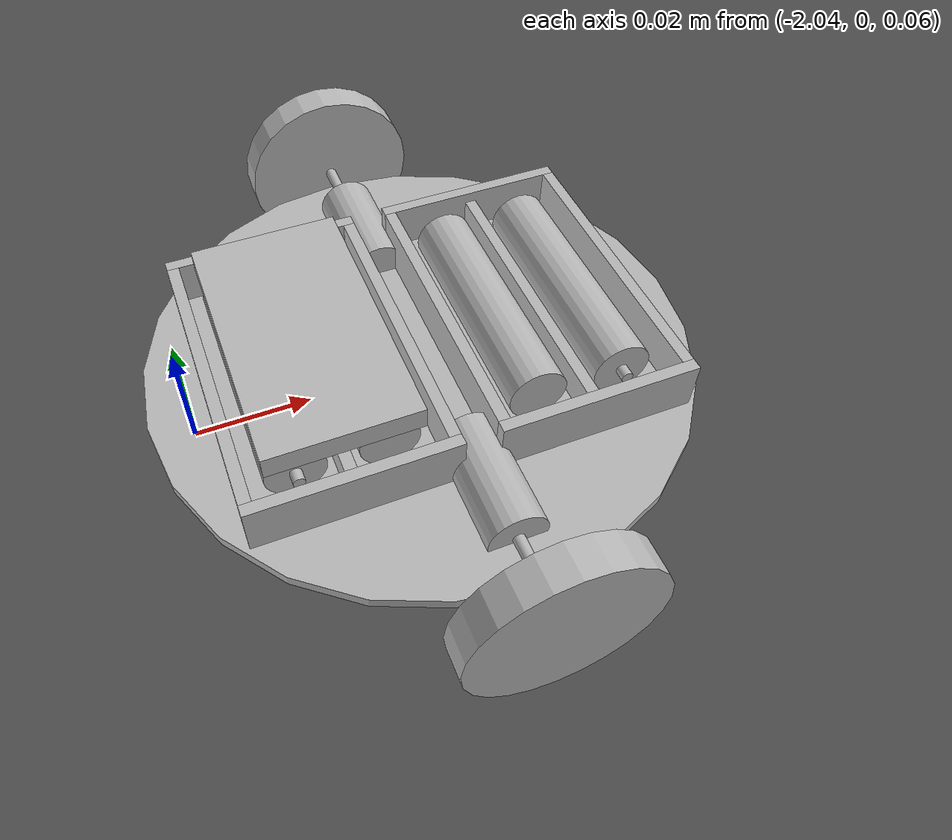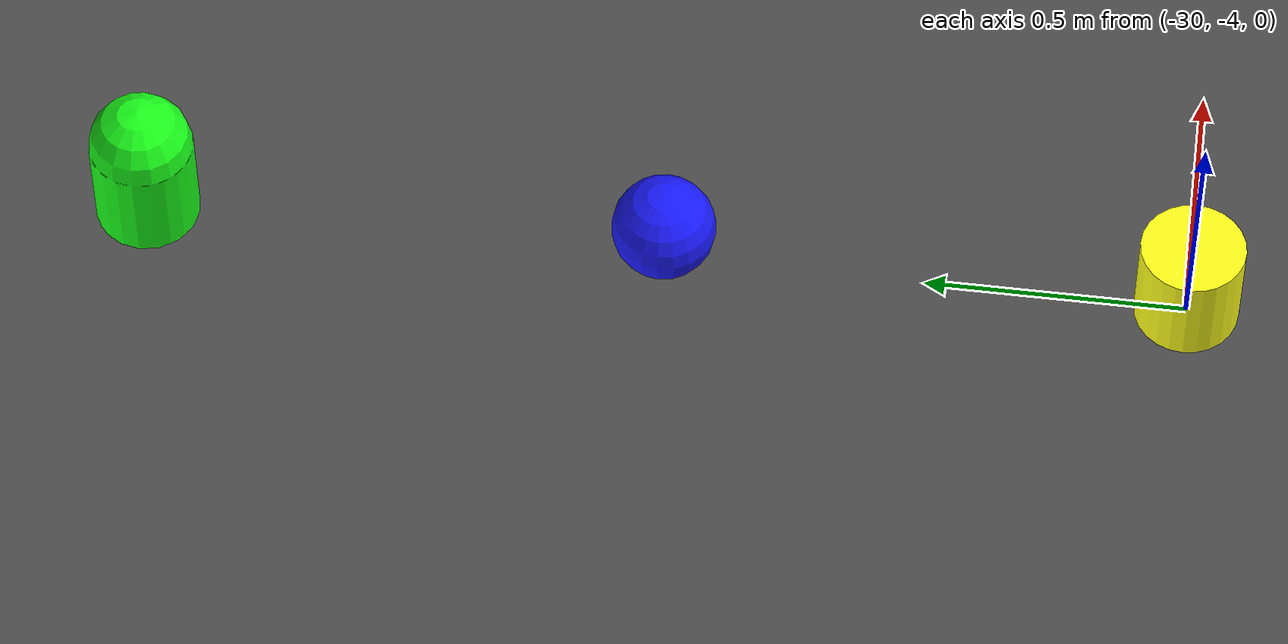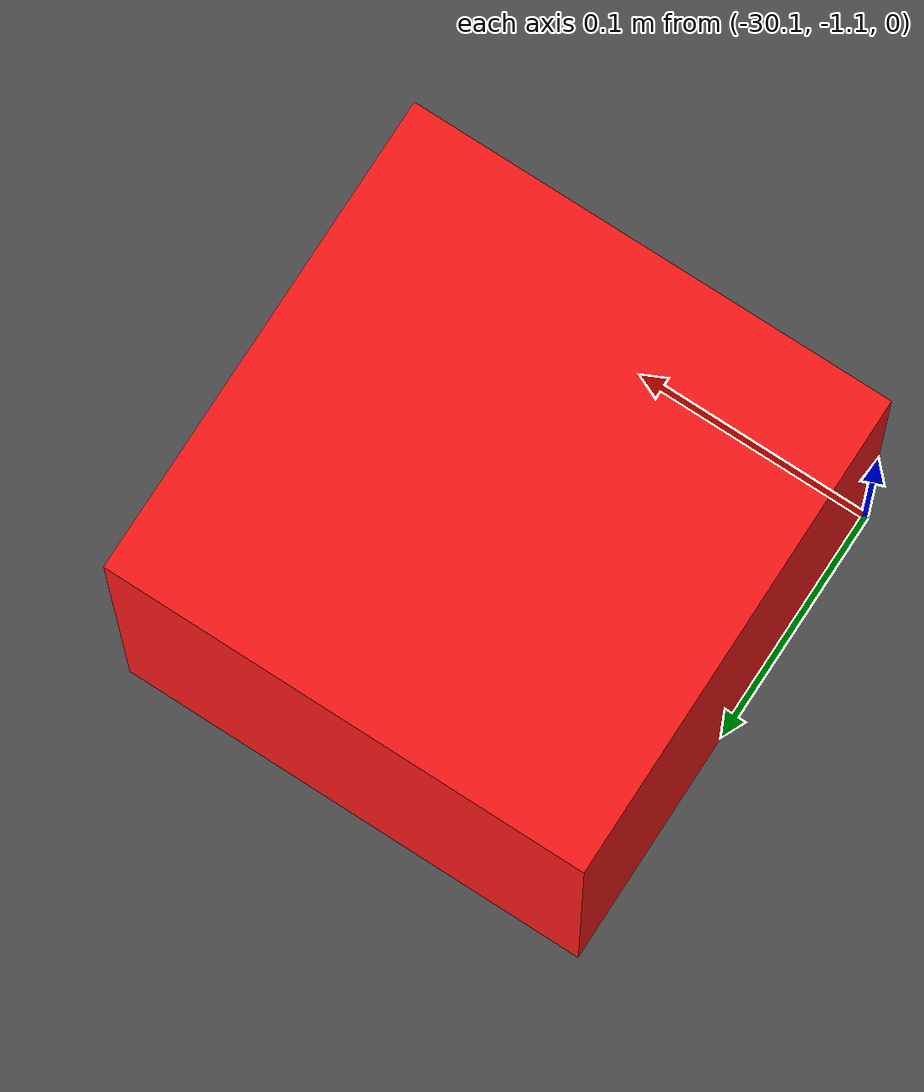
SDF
<?xml version="1.0"?>
<sdf version="1.10">
    <world name="catching_robot_world">
        <physics name="default_physics" type="dart">
            <max_step_size>0.001</max_step_size>
            <real_time_factor>1</real_time_factor>
            <real_time_update_rate>1000</real_time_update_rate>
        </physics>

        <plugin
            filename="gz-sim-physics-system"
            name="gz::sim::systems::Physics">
        </plugin>
        <plugin
            filename="gz-sim-sensors-system"
            name="gz::sim::systems::Sensors">
        </plugin>
        <plugin
            filename="gz-sim-scene-broadcaster-system"
            name="gz::sim::systems::SceneBroadcaster">
        </plugin>
        <plugin
            filename="gz-sim-user-commands-system"
            name="gz::sim::systems::UserCommands">
        </plugin>

        <gui>
        <camera name="observation_camera">
                <view_controller>orbit</view_controller>
                <projection_type>perspective</projection_type>
				<track_visual>
					<name>3pi_robot</name>
					<static>1</static>
					<xyz>-0.01 0 2</xyz>
                    <inherit_yaw>0</inherit_yaw>
				</track_visual>
			</camera>
		</gui>

        <light type="directional" name="sun">
            <cast_shadows>0</cast_shadows>
            <pose>0 0 10 0 0 0</pose>
            <diffuse>0.8 0.8 0.8 1</diffuse>
            <specular>0.2 0.2 0.2 1</specular>
            <attenuation>
                <range>1000</range>
                <constant>0.9</constant>
                <linear>0.01</linear>
                <quadratic>0.001</quadratic>
            </attenuation>
            <direction>1  0 -0.7</direction>
        </light>

        <include>
            <uri>model://cr_models//arena_ground_plane</uri>
        </include>

        <include>
            <pose>0 0 -0.3 0 0 0</pose>
            <uri>model:://ground_plane</uri>
        </include>

        <include>
            <pose>-30 -1 -0.25 0 0 0</pose>
            <uri>model://cr_models//red_runner_robot</uri>
        </include>

        <include>
            <pose>-30 -2 -0.25 0 0 0</pose>
            <uri>model://cr_models//green_runner_robot</uri>
        </include>

        <include>
            <pose>-30 -3 -0.25 0 0 0</pose>
            <uri>model://cr_models//blue_runner_robot</uri>
        </include>

        <include>
            <pose>-30 -4 -0.25 0 0 0</pose>
            <uri>model://cr_models//yellow_runner_robot</uri>
        </include>

        <include>
            <pose>-2 0 0.05 0 0 0</pose>
            <uri>model://cr_models//catcher_robot</uri>
        </include>
    </world>
</sdf>

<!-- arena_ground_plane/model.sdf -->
<sdf version="1.11">
	<model name="arena_ground_plane">
		<static>1</static>
		<pose>0 0 0 0 0 0</pose>
		<link name="link">
			<collision name="collision">
				<geometry>
					<plane>
						<normal>0 0 1</normal>
						<size>100 100</size>
					</plane>
				</geometry>
                                <surface><friction><ode>
                                <mu>10000000</mu>
                                <mu2>10000000</mu2>
                                </ode></friction></surface>
			</collision>
			<visual name="visual">
				<geometry>
					<plane>
						<normal>0 0 1</normal>
						<size>100 100</size>
					</plane>
				</geometry>
				<material>
					<ambient>0.3 0.3 0.3 1</ambient>
					<diffuse>0.3 0.3 0.3 1</diffuse>
					<specular>0.3 0.3 0.3 1</specular>
					<pbr>
						<metal>
	        				<albedo_map>arena/arena_ground_floor_tiny.png</albedo_map>
						</metal>
					</pbr>
				</material>
			</visual>
		</link>
	</model>

</sdf>

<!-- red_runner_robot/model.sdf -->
<sdf version="1.11">
	<model name="red_runner_robot">
		<static>0</static>
		<pose>0 0 0 0 0 0</pose>
		<!-- LINKS - LINKS - LINKS -->
		<link name="blade_link">
			<pose>0 0 0.013 0 0 0</pose>
			<inertial>
				<mass>0.005</mass>
				<pose>0 0 0.001 0 0 0</pose>
				<inertia>
					<ixx>2.92e-06</ixx>
					<ixy>0</ixy>
					<ixz>0</ixz>
					<iyy>2.92e-06</iyy>
					<iyz>0</iyz>
					<izz>5.52e-06</izz>
				</inertia>
			</inertial>
			<self_collide>0</self_collide>
			<enable_wind>0</enable_wind>
			<kinematic>0</kinematic>
			<gravity>1</gravity>
			<visual name="body_visual">
				<pose>0 0 0.001 0 0 0</pose>
				<geometry>
					<cylinder>
						<radius>0.047</radius>
						<length>0.002</length>
					</cylinder>
				</geometry>
				<transparency>0</transparency>
				<cast_shadows>1</cast_shadows>
			</visual>
		</link>
		<link name="battery_b_lr_link">
			<pose>-0.0275 0.02 0.02 1.570796 0 0</pose>
			<inertial>
				<mass>0.00756</mass>
				<pose>0 0 0.02 0 0 0</pose>
				<inertia>
					<ixx>1.06e-06</ixx>
					<ixy>0</ixy>
					<ixz>0</ixz>
					<iyy>1.06e-06</iyy>
					<iyz>0</iyz>
					<izz>9.5e-08</izz>
				</inertia>
			</inertial>
			<self_collide>0</self_collide>
			<enable_wind>0</enable_wind>
			<kinematic>0</kinematic>
			<gravity>1</gravity>
			<visual name="body_visual">
				<pose>0 0 0.02 0 0 0</pose>
				<geometry>
					<cylinder>
						<radius>0.005</radius>
						<length>0.04</length>
					</cylinder>
				</geometry>
				<transparency>0</transparency>
				<cast_shadows>1</cast_shadows>
			</visual>
			<visual name="head_visual">
				<pose>0 0 0.041 0 0 0</pose>
				<geometry>
					<cylinder>
						<radius>0.001</radius>
						<length>0.002</length>
					</cylinder>
				</geometry>
				<transparency>0</transparency>
				<cast_shadows>1</cast_shadows>
			</visual>
		</link>
		<link name="battery_b_rl_link">
			<pose>-0.0125 -0.02 0.02 -1.570796 0 0</pose>
			<inertial>
				<mass>0.00756</mass>
				<pose>0 0 0.02 0 0 0</pose>
				<inertia>
					<ixx>1.06e-06</ixx>
					<ixy>0</ixy>
					<ixz>0</ixz>
					<iyy>1.06e-06</iyy>
					<iyz>0</iyz>
					<izz>9.5e-08</izz>
				</inertia>
			</inertial>
			<self_collide>0</self_collide>
			<enable_wind>0</enable_wind>
			<kinematic>0</kinematic>
			<gravity>1</gravity>
			<visual name="body_visual">
				<pose>0 0 0.02 0 0 0</pose>
				<geometry>
					<cylinder>
						<radius>0.005</radius>
						<length>0.04</length>
					</cylinder>
				</geometry>
				<transparency>0</transparency>
				<cast_shadows>1</cast_shadows>
			</visual>
			<visual name="head_visual">
				<pose>0 0 0.041 0 0 0</pose>
				<geometry>
					<cylinder>
						<radius>0.001</radius>
						<length>0.002</length>
					</cylinder>
				</geometry>
				<transparency>0</transparency>
				<cast_shadows>1</cast_shadows>
			</visual>
		</link>
		<link name="box_b_link">
			<pose>-0.02 0 0.014 0 0 1.570796</pose>
			<inertial>
				<mass>0.00101</mass>
				<pose>0 0 0.005 0 0 0</pose>
				<inertia>
					<ixx>1.06e-07</ixx>
					<ixy>0</ixy>
					<ixz>0</ixz>
					<iyy>2.19e-07</iyy>
					<iyz>0</iyz>
					<izz>3.08e-07</izz>
				</inertia>
			</inertial>
			<self_collide>0</self_collide>
			<enable_wind>0</enable_wind>
			<kinematic>0</kinematic>
			<gravity>1</gravity>
			<visual name="front_visual">
				<pose>0 0.016 0.005 0 0 0</pose>
				<geometry>
					<box>
						<size>0.05 0.002 0.01</size>
					</box>
				</geometry>
				<transparency>0</transparency>
				<cast_shadows>1</cast_shadows>
			</visual>
			<visual name="back_visual">
				<pose>0 -0.016 0.005 0 0 0</pose>
				<geometry>
					<box>
						<size>0.05 0.002 0.01</size>
					</box>
				</geometry>
				<transparency>0</transparency>
				<cast_shadows>1</cast_shadows>
			</visual>
			<visual name="bottom_visual">
				<pose>0 0 0.001 0 0 0</pose>
				<geometry>
					<box>
						<size>0.05 0.03 0.002</size>
					</box>
				</geometry>
				<transparency>0</transparency>
				<cast_shadows>1</cast_shadows>
			</visual>
			<visual name="left_visual">
				<pose>-0.026 0 0.005 0 0 0</pose>
				<geometry>
					<box>
						<size>0.002 0.034 0.01</size>
					</box>
				</geometry>
				<transparency>0</transparency>
				<cast_shadows>1</cast_shadows>
			</visual>
			<visual name="middle_visual">
				<pose>0 0 0.005 0 0 0</pose>
				<geometry>
					<box>
						<size>0.05 0.002 0.006</size>
					</box>
				</geometry>
				<transparency>0</transparency>
				<cast_shadows>1</cast_shadows>
			</visual>
			<visual name="right_visual">
				<pose>0.026 0 0.005 0 0 0</pose>
				<geometry>
					<box>
						<size>0.002 0.034 0.01</size>
					</box>
				</geometry>
				<transparency>0</transparency>
				<cast_shadows>1</cast_shadows>
			</visual>
		</link>
		<link name="battery_f_lr_link">
			<pose>0.0275 0.02 0.02 1.570796 0 0</pose>
			<inertial>
				<mass>0.00756</mass>
				<pose>0 0 0.02 0 0 0</pose>
				<inertia>
					<ixx>1.06e-06</ixx>
					<ixy>0</ixy>
					<ixz>0</ixz>
					<iyy>1.06e-06</iyy>
					<iyz>0</iyz>
					<izz>9.5e-08</izz>
				</inertia>
			</inertial>
			<self_collide>0</self_collide>
			<enable_wind>0</enable_wind>
			<kinematic>0</kinematic>
			<gravity>1</gravity>
			<visual name="body_visual">
				<pose>0 0 0.02 0 0 0</pose>
				<geometry>
					<cylinder>
						<radius>0.005</radius>
						<length>0.04</length>
					</cylinder>
				</geometry>
				<transparency>0</transparency>
				<cast_shadows>1</cast_shadows>
			</visual>
			<visual name="head_visual">
				<pose>0 0 0.041 0 0 0</pose>
				<geometry>
					<cylinder>
						<radius>0.001</radius>
						<length>0.002</length>
					</cylinder>
				</geometry>
				<transparency>0</transparency>
				<cast_shadows>1</cast_shadows>
			</visual>
		</link>
		<link name="battery_f_rl_link">
			<pose>0.0125 -0.02 0.02 -1.570796 0 0</pose>
			<inertial>
				<mass>0.00756</mass>
				<pose>0 0 0.02 0 0 0</pose>
				<inertia>
					<ixx>1.06e-06</ixx>
					<ixy>0</ixy>
					<ixz>0</ixz>
					<iyy>1.06e-06</iyy>
					<iyz>0</iyz>
					<izz>9.5e-08</izz>
				</inertia>
			</inertial>
			<self_collide>0</self_collide>
			<enable_wind>0</enable_wind>
			<kinematic>0</kinematic>
			<gravity>1</gravity>
			<visual name="body_visual">
				<pose>0 0 0.02 0 0 0</pose>
				<geometry>
					<cylinder>
						<radius>0.005</radius>
						<length>0.04</length>
					</cylinder>
				</geometry>
				<transparency>0</transparency>
				<cast_shadows>1</cast_shadows>
			</visual>
			<visual name="head_visual">
				<pose>0 0 0.041 0 0 0</pose>
				<geometry>
					<cylinder>
						<radius>0.001</radius>
						<length>0.002</length>
					</cylinder>
				</geometry>
				<transparency>0</transparency>
				<cast_shadows>1</cast_shadows>
			</visual>
		</link>
		<link name="box_f_link">
			<pose>0.02 0 0.014 0 0 -1.570796</pose>
			<inertial>
				<mass>0.00101</mass>
				<pose>0 0 0.005 0 0 0</pose>
				<inertia>
					<ixx>1.06e-07</ixx>
					<ixy>0</ixy>
					<ixz>0</ixz>
					<iyy>2.19e-07</iyy>
					<iyz>0</iyz>
					<izz>3.08e-07</izz>
				</inertia>
			</inertial>
			<self_collide>0</self_collide>
			<enable_wind>0</enable_wind>
			<kinematic>0</kinematic>
			<gravity>1</gravity>
			<visual name="right_visual">
				<pose>0.026 0 0.005 0 0 0</pose>
				<geometry>
					<box>
						<size>0.002 0.034 0.01</size>
					</box>
				</geometry>
				<transparency>0</transparency>
				<cast_shadows>1</cast_shadows>
			</visual>
			<visual name="front_visual">
				<pose>0 0.016 0.005 0 0 0</pose>
				<geometry>
					<box>
						<size>0.05 0.002 0.01</size>
					</box>
				</geometry>
				<transparency>0</transparency>
				<cast_shadows>1</cast_shadows>
			</visual>
			<visual name="bottom_visual">
				<pose>0 0 0.001 0 0 0</pose>
				<geometry>
					<box>
						<size>0.05 0.03 0.002</size>
					</box>
				</geometry>
				<transparency>0</transparency>
				<cast_shadows>1</cast_shadows>
			</visual>
			<visual name="middle_visual">
				<pose>0 0 0.005 0 0 0</pose>
				<geometry>
					<box>
						<size>0.05 0.002 0.006</size>
					</box>
				</geometry>
				<transparency>0</transparency>
				<cast_shadows>1</cast_shadows>
			</visual>
			<visual name="left_visual">
				<pose>-0.026 0 0.005 0 0 0</pose>
				<geometry>
					<box>
						<size>0.002 0.034 0.01</size>
					</box>
				</geometry>
				<transparency>0</transparency>
				<cast_shadows>1</cast_shadows>
			</visual>
			<visual name="back_visual">
				<pose>0 -0.016 0.005 0 0 0</pose>
				<geometry>
					<box>
						<size>0.05 0.002 0.01</size>
					</box>
				</geometry>
				<transparency>0</transparency>
				<cast_shadows>1</cast_shadows>
			</visual>
		</link>
		<link name="caster_link">
			<pose>-0.04 0 0 0 0 0</pose>
			<inertial>
				<mass>0.00144</mass>
				<pose>0 0 0.0065 0 0 0</pose>
				<inertia>
					<ixx>2.4e-08</ixx>
					<ixy>0</ixy>
					<ixz>0</ixz>
					<iyy>2.4e-08</iyy>
					<iyz>0</iyz>
					<izz>2.4e-08</izz>
				</inertia>
			</inertial>
			<self_collide>0</self_collide>
			<enable_wind>0</enable_wind>
			<kinematic>0</kinematic>
			<gravity>1</gravity>
			<visual name="body_visual">
				<pose>0 0 0.0065 0 0 0</pose>
				<geometry>
					<sphere>
						<radius>0.0065</radius>
					</sphere>
				</geometry>
				<transparency>0</transparency>
				<cast_shadows>1</cast_shadows>
			</visual>
			<collision name="body_collision">
				<laser_retro>0</laser_retro>
				<max_contacts>10</max_contacts>
				<pose>0 0 0.0065 0 0 0</pose>
				<geometry>
					<sphere>
						<radius>0.0065</radius>
					</sphere>
				</geometry>
				<surface>
					<friction>
						<ode>
							<mu>1</mu>
							<mu2>0.5</mu2>
							<fdir1>0 0 0</fdir1>
							<slip1>0</slip1>
							<slip2>0</slip2>
						</ode>
						<torsional>
							<coefficient>0.75</coefficient>
							<use_patch_radius>0</use_patch_radius>
							<surface_radius>0.0065</surface_radius>
							<ode>
								<slip>0</slip>
							</ode>
						</torsional>
					</friction>
					<contact>
						<ode>
							<soft_cfm>0</soft_cfm>
							<soft_erp>0.2</soft_erp>
							<kp>1e+13</kp>
							<kd>1</kd>
							<max_vel>1</max_vel>
							<min_depth>0.001</min_depth>
						</ode>
					</contact>
				</surface>
			</collision>
		</link>
		<link name="wheel_l_link">
			<pose>0 -0.05 0.016 1.570796 0 0</pose>
			<inertial>
				<mass>0.00311</mass>
				<pose>0 0 0.003 0 0 0</pose>
				<inertia>
					<ixx>2.08e-07</ixx>
					<ixy>0</ixy>
					<ixz>0</ixz>
					<iyy>2.08e-07</iyy>
					<iyz>0</iyz>
					<izz>3.98e-07</izz>
				</inertia>
			</inertial>
			<self_collide>0</self_collide>
			<enable_wind>0</enable_wind>
			<kinematic>0</kinematic>
			<gravity>1</gravity>
			<visual name="body_visual">
				<pose>0 0 0.003 0 0 0</pose>
				<geometry>
					<cylinder>
						<radius>0.016</radius>
						<length>0.006</length>
					</cylinder>
				</geometry>
				<transparency>0</transparency>
				<cast_shadows>1</cast_shadows>
			</visual>
			<collision name="body_collision">
				<laser_retro>0</laser_retro>
				<max_contacts>10</max_contacts>
				<pose>0 0 0.003 0 0 0</pose>
				<geometry>
					<cylinder>
						<radius>0.016</radius>
						<length>0.006</length>
					</cylinder>
				</geometry>
				<surface>
					<friction>
						<ode>
							<mu>20000000</mu>
							<mu2>10000000</mu2>
							<slip1>0</slip1>
							<slip2>0</slip2>
						</ode>
						<torsional>
							<coefficient>15</coefficient>
							<use_patch_radius>0</use_patch_radius>
							<surface_radius>0.016</surface_radius>
							<ode>
								<slip>0</slip>
							</ode>
						</torsional>
					</friction>
					<contact>
						<ode>
							<soft_cfm>0</soft_cfm>
							<soft_erp>0.2</soft_erp>
							<kp>1e+13</kp>
							<kd>1</kd>
							<max_vel>1</max_vel>
							<min_depth>0.001</min_depth>
						</ode>
					</contact>
				</surface>
			</collision>
		</link>
		<link name="motor_l_link">
			<pose>0 -0.02 0.016 1.570796 0 0</pose>
			<inertial>
				<mass>0.03158</mass>
				<pose>0 0 0.01 0 0 0</pose>
				<inertia>
					<ixx>1.25e-06</ixx>
					<ixy>0</ixy>
					<ixz>0</ixz>
					<iyy>1.25e-06</iyy>
					<iyz>0</iyz>
					<izz>3.95e-07</izz>
				</inertia>
			</inertial>
			<self_collide>0</self_collide>
			<enable_wind>0</enable_wind>
			<kinematic>0</kinematic>
			<gravity>1</gravity>
			<visual name="body_visual">
				<pose>0 0 0.01 0 0 0</pose>
				<geometry>
					<cylinder>
						<radius>0.005</radius>
						<length>0.02</length>
					</cylinder>
				</geometry>
				<transparency>0</transparency>
				<cast_shadows>1</cast_shadows>
			</visual>
			<visual name="axis_visual">
				<pose>0 0 0.025 0 0 0</pose>
				<geometry>
					<cylinder>
						<radius>0.001</radius>
						<length>0.01</length>
					</cylinder>
				</geometry>
				<transparency>0</transparency>
				<cast_shadows>1</cast_shadows>
			</visual>
		</link>
		<link name="wheel_r_link">
			<pose>0 0.05 0.016 -1.570796 0 0</pose>
			<inertial>
				<mass>0.00311</mass>
				<pose>0 0 0.003 0 0 0</pose>
				<inertia>
					<ixx>2.08e-07</ixx>
					<ixy>0</ixy>
					<ixz>0</ixz>
					<iyy>2.08e-07</iyy>
					<iyz>0</iyz>
					<izz>3.98e-07</izz>
				</inertia>
			</inertial>
			<self_collide>0</self_collide>
			<enable_wind>0</enable_wind>
			<kinematic>0</kinematic>
			<gravity>1</gravity>
			<visual name="body_visual">
				<pose>0 0 0.003 0 0 0</pose>
				<geometry>
					<cylinder>
						<radius>0.016</radius>
						<length>0.006</length>
					</cylinder>
				</geometry>
				<transparency>0</transparency>
				<cast_shadows>1</cast_shadows>
			</visual>
			<collision name="body_collision">
				<laser_retro>0</laser_retro>
				<max_contacts>10</max_contacts>
				<pose>0 0 0.003 0 0 0</pose>
				<geometry>
					<cylinder>
						<radius>0.016</radius>
						<length>0.006</length>
					</cylinder>
				</geometry>
				<surface>
					<friction>
						<ode>
							<mu>2000000</mu>
							<mu2>1000000</mu2>
							<slip1>0</slip1>
							<slip2>0</slip2>
						</ode>
						<torsional>
							<coefficient>15</coefficient>
							<use_patch_radius>0</use_patch_radius>
							<surface_radius>0.016</surface_radius>
							<ode>
								<slip>0</slip>
							</ode>
						</torsional>
					</friction>
					<contact>
						<ode>
							<soft_cfm>0</soft_cfm>
							<soft_erp>0.2</soft_erp>
							<kp>1e+13</kp>
							<kd>1</kd>
							<max_vel>1</max_vel>
							<min_depth>0.001</min_depth>
						</ode>
					</contact>
				</surface>
			</collision>
		</link>
		<link name="motor_r_link">
			<pose>0 0.02 0.016 -1.570796 0 0</pose>
			<inertial>
				<mass>0.03158</mass>
				<pose>0 0 0.01 0 0 0</pose>
				<inertia>
					<ixx>1.25e-06</ixx>
					<ixy>0</ixy>
					<ixz>0</ixz>
					<iyy>1.25e-06</iyy>
					<iyz>0</iyz>
					<izz>3.95e-07</izz>
				</inertia>
			</inertial>
			<self_collide>0</self_collide>
			<enable_wind>0</enable_wind>
			<kinematic>0</kinematic>
			<gravity>1</gravity>
			<visual name="body_visual">
				<pose>0 0 0.01 0 0 0</pose>
				<geometry>
					<cylinder>
						<radius>0.005</radius>
						<length>0.02</length>
					</cylinder>
				</geometry>
				<transparency>0</transparency>
				<cast_shadows>1</cast_shadows>
			</visual>
			<visual name="axis_visual">
				<pose>0 0 0.025 0 0 0</pose>
				<geometry>
					<cylinder>
						<radius>0.001</radius>
						<length>0.01</length>
					</cylinder>
				</geometry>
				<transparency>0</transparency>
				<cast_shadows>1</cast_shadows>
			</visual>
		</link>
		<link name="display_link">
			<pose>-0.02 0 0.025 0 0 1.570796</pose>
			<inertial>
				<mass>0.01164</mass>
				<pose>0 0 0.002 0 0 0</pose>
				<inertia>
					<ixx>6.22e-07</ixx>
					<ixy>0</ixy>
					<ixz>0</ixz>
					<iyy>1.98e-06</iyy>
					<iyz>0</iyz>
					<izz>2.57e-06</izz>
				</inertia>
			</inertial>
			<self_collide>0</self_collide>
			<enable_wind>0</enable_wind>
			<kinematic>0</kinematic>
			<gravity>1</gravity>
			<visual name="body_visual">
				<pose>0 0 0.002 0 0 0</pose>
				<geometry>
					<box>
						<size>0.045 0.025 0.004</size>
					</box>
				</geometry>
				<transparency>0</transparency>
				<cast_shadows>1</cast_shadows>
			</visual>
		</link>
		<link name="visual_object_link">
			<pose>0 0 0.35 0 0 0</pose>
			<kinematic>true</kinematic>
			<inertial>
				<mass>1e-12</mass>
				<inertia>
					<ixx>0</ixx>
					<ixy>0</ixy>
					<ixz>0</ixz>
					<iyy>0</iyy>
					<iyz>0</iyz>
					<izz>0</izz>
				</inertia>
			</inertial>
			<visual name="red_cube">
				<pose>0 0 0 0 0 0</pose>
				<geometry>
					<box>
						<size>0.2 0.2 0.2</size>
					</box>
				</geometry>
				<material>
					<ambient>1.0 0.1 0.1 1</ambient>
					<diffuse>1.0 0.1 0.1 1</diffuse>
				</material>
			</visual>
		</link>

		<!-- JOINTS - JOINTS - JOINTS -->
		<joint name="battery_b_lr_joint" type="fixed">
			<parent>box_b_link</parent>
			<child>battery_b_lr_link</child>
			<pose>0 0 0 0 0 0</pose>
			<physics>
				<ode>
					<limit>
						<cfm>0</cfm>
						<erp>0.2</erp>
					</limit>
					<suspension>
						<cfm>0</cfm>
						<erp>0.2</erp>
					</suspension>
				</ode>
			</physics>
		</joint>
		<joint name="battery_b_rl_joint" type="fixed">
			<parent>box_b_link</parent>
			<child>battery_b_rl_link</child>
			<pose>0 0 0 0 0 0</pose>
			<physics>
				<ode>
					<limit>
						<cfm>0</cfm>
						<erp>0.2</erp>
					</limit>
					<suspension>
						<cfm>0</cfm>
						<erp>0.2</erp>
					</suspension>
				</ode>
			</physics>
		</joint>
		<joint name="battery_f_lr_joint" type="fixed">
			<parent>box_f_link</parent>
			<child>battery_f_lr_link</child>
			<pose>0 0 0 0 0 0</pose>
			<physics>
				<ode>
					<limit>
						<cfm>0</cfm>
						<erp>0.2</erp>
					</limit>
					<suspension>
						<cfm>0</cfm>
						<erp>0.2</erp>
					</suspension>
				</ode>
			</physics>
		</joint>
		<joint name="box_b_joint" type="fixed">
			<parent>blade_link</parent>
			<child>box_b_link</child>
			<pose>0 0 0 0 0 0</pose>
			<physics>
				<ode>
					<limit>
						<cfm>0</cfm>
						<erp>0.2</erp>
					</limit>
					<suspension>
						<cfm>0</cfm>
						<erp>0.2</erp>
					</suspension>
				</ode>
			</physics>
		</joint>
		<joint name="battery_f_rl_joint" type="fixed">
			<parent>box_f_link</parent>
			<child>battery_f_rl_link</child>
			<pose>0 0 0 0 0 0</pose>
			<physics>
				<ode>
					<limit>
						<cfm>0</cfm>
						<erp>0.2</erp>
					</limit>
					<suspension>
						<cfm>0</cfm>
						<erp>0.2</erp>
					</suspension>
				</ode>
			</physics>
		</joint>
		<joint name="box_f_joint" type="fixed">
			<parent>blade_link</parent>
			<child>box_f_link</child>
			<pose>0 0 0 0 0 0</pose>
			<physics>
				<ode>
					<limit>
						<cfm>0</cfm>
						<erp>0.2</erp>
					</limit>
					<suspension>
						<cfm>0</cfm>
						<erp>0.2</erp>
					</suspension>
				</ode>
			</physics>
		</joint>
		<joint name="caster_joint" type="ball">
			<parent>blade_link</parent>
			<child>caster_link</child>
			<pose>0 0 0.0065 0 0 0</pose>
			<physics>
				<ode>
					<limit>
						<cfm>0</cfm>
						<erp>0.2</erp>
					</limit>
					<suspension>
						<cfm>0</cfm>
						<erp>0.2</erp>
					</suspension>
				</ode>
			</physics>
		</joint>
		<joint name="left_axis_joint" type="revolute">
			<parent>blade_link</parent>
			<child>wheel_l_link</child>
			<pose>0 0 0 0 0 0</pose>
			<axis>
				<xyz>0 0 -1</xyz>
			</axis>
			<physics>
				<ode>
					<cfm>0</cfm>
					<erp>0.2</erp>
					<limit>
						<cfm>0</cfm>
						<erp>0.2</erp>
					</limit>
					<suspension>
						<cfm>0</cfm>
						<erp>0.2</erp>
					</suspension>
				</ode>
			</physics>
		</joint>
		<joint name="motor_l_joint" type="fixed">
			<parent>blade_link</parent>
			<child>motor_l_link</child>
			<pose>0 0 0 0 0 0</pose>
		</joint>
		<joint name="right_axis_joint" type="revolute">
			<parent>blade_link</parent>
			<child>wheel_r_link</child>
			<pose>0 0 0 0 0 0</pose>
			<axis>
				<xyz>0 0 1</xyz>
			</axis>
			<physics>
				<ode>
					<cfm>0</cfm>
					<erp>0.2</erp>
					<limit>
						<cfm>0</cfm>
						<erp>0.2</erp>
					</limit>
					<suspension>
						<cfm>0</cfm>
						<erp>0.2</erp>
					</suspension>
				</ode>
			</physics>
		</joint>
		<joint name="motor_r_joint" type="fixed">
			<parent>blade_link</parent>
			<child>motor_r_link</child>
			<pose>0 0 0 0 0 0</pose>
		</joint>
		<joint name="display_joint" type="fixed">
			<parent>box_b_link</parent>
			<child>display_link</child>
			<pose>0 0 0 0 0 0</pose>
		</joint>
		<joint name="visual_object_joint" type="fixed">
			<parent>box_f_link</parent>
			<child>visual_object_link</child>
			<pose>0 0 0 0 0 0</pose>
		</joint>

		<!-- PLUGINS - PLUGINS - PLUGINS -->
		<plugin filename="gz-sim-diff-drive-system" name="gz::sim::systems::DiffDrive">
			<topic>/red_runner_robot/motor</topic>
			<left_joint>left_axis_joint</left_joint>
			<right_joint>right_axis_joint</right_joint>
			<wheel_separation>0.1</wheel_separation>
			<wheel_radius>0.016</wheel_radius>
			<min_velocity>-1.0</min_velocity>
			<max_velocity>+1.0</max_velocity>
			<min_acceleration>-100000000.5</min_acceleration>
			<max_acceleration>+100000000.5</max_acceleration>
			<min_jerk>-100000000000.0</min_jerk>
			<max_jerk>+100000000000.0</max_jerk>
			<odom_topic>/vehicle/odo</odom_topic>
			<odom_publish_frequency>5</odom_publish_frequency>
		</plugin>
	</model>
</sdf>

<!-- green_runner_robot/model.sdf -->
<sdf version="1.11">
	<model name="green_runner_robot">
		<static>0</static>
		<pose>0 0 0 0 0 0</pose>
		<!-- LINKS - LINKS - LINKS -->
		<link name="blade_link">
			<pose>0 0 0.013 0 0 0</pose>
			<inertial>
				<mass>0.005</mass>
				<pose>0 0 0.001 0 0 0</pose>
				<inertia>
					<ixx>2.92e-06</ixx>
					<ixy>0</ixy>
					<ixz>0</ixz>
					<iyy>2.92e-06</iyy>
					<iyz>0</iyz>
					<izz>5.52e-06</izz>
				</inertia>
			</inertial>
			<self_collide>0</self_collide>
			<enable_wind>0</enable_wind>
			<kinematic>0</kinematic>
			<gravity>1</gravity>
			<visual name="body_visual">
				<pose>0 0 0.001 0 0 0</pose>
				<geometry>
					<cylinder>
						<radius>0.047</radius>
						<length>0.002</length>
					</cylinder>
				</geometry>
				<transparency>0</transparency>
				<cast_shadows>1</cast_shadows>
			</visual>
		</link>
		<link name="battery_b_lr_link">
			<pose>-0.0275 0.02 0.02 1.570796 0 0</pose>
			<inertial>
				<mass>0.00756</mass>
				<pose>0 0 0.02 0 0 0</pose>
				<inertia>
					<ixx>1.06e-06</ixx>
					<ixy>0</ixy>
					<ixz>0</ixz>
					<iyy>1.06e-06</iyy>
					<iyz>0</iyz>
					<izz>9.5e-08</izz>
				</inertia>
			</inertial>
			<self_collide>0</self_collide>
			<enable_wind>0</enable_wind>
			<kinematic>0</kinematic>
			<gravity>1</gravity>
			<visual name="body_visual">
				<pose>0 0 0.02 0 0 0</pose>
				<geometry>
					<cylinder>
						<radius>0.005</radius>
						<length>0.04</length>
					</cylinder>
				</geometry>
				<transparency>0</transparency>
				<cast_shadows>1</cast_shadows>
			</visual>
			<visual name="head_visual">
				<pose>0 0 0.041 0 0 0</pose>
				<geometry>
					<cylinder>
						<radius>0.001</radius>
						<length>0.002</length>
					</cylinder>
				</geometry>
				<transparency>0</transparency>
				<cast_shadows>1</cast_shadows>
			</visual>
		</link>
		<link name="battery_b_rl_link">
			<pose>-0.0125 -0.02 0.02 -1.570796 0 0</pose>
			<inertial>
				<mass>0.00756</mass>
				<pose>0 0 0.02 0 0 0</pose>
				<inertia>
					<ixx>1.06e-06</ixx>
					<ixy>0</ixy>
					<ixz>0</ixz>
					<iyy>1.06e-06</iyy>
					<iyz>0</iyz>
					<izz>9.5e-08</izz>
				</inertia>
			</inertial>
			<self_collide>0</self_collide>
			<enable_wind>0</enable_wind>
			<kinematic>0</kinematic>
			<gravity>1</gravity>
			<visual name="body_visual">
				<pose>0 0 0.02 0 0 0</pose>
				<geometry>
					<cylinder>
						<radius>0.005</radius>
						<length>0.04</length>
					</cylinder>
				</geometry>
				<transparency>0</transparency>
				<cast_shadows>1</cast_shadows>
			</visual>
			<visual name="head_visual">
				<pose>0 0 0.041 0 0 0</pose>
				<geometry>
					<cylinder>
						<radius>0.001</radius>
						<length>0.002</length>
					</cylinder>
				</geometry>
				<transparency>0</transparency>
				<cast_shadows>1</cast_shadows>
			</visual>
		</link>
		<link name="box_b_link">
			<pose>-0.02 0 0.014 0 0 1.570796</pose>
			<inertial>
				<mass>0.00101</mass>
				<pose>0 0 0.005 0 0 0</pose>
				<inertia>
					<ixx>1.06e-07</ixx>
					<ixy>0</ixy>
					<ixz>0</ixz>
					<iyy>2.19e-07</iyy>
					<iyz>0</iyz>
					<izz>3.08e-07</izz>
				</inertia>
			</inertial>
			<self_collide>0</self_collide>
			<enable_wind>0</enable_wind>
			<kinematic>0</kinematic>
			<gravity>1</gravity>
			<visual name="front_visual">
				<pose>0 0.016 0.005 0 0 0</pose>
				<geometry>
					<box>
						<size>0.05 0.002 0.01</size>
					</box>
				</geometry>
				<transparency>0</transparency>
				<cast_shadows>1</cast_shadows>
			</visual>
			<visual name="back_visual">
				<pose>0 -0.016 0.005 0 0 0</pose>
				<geometry>
					<box>
						<size>0.05 0.002 0.01</size>
					</box>
				</geometry>
				<transparency>0</transparency>
				<cast_shadows>1</cast_shadows>
			</visual>
			<visual name="bottom_visual">
				<pose>0 0 0.001 0 0 0</pose>
				<geometry>
					<box>
						<size>0.05 0.03 0.002</size>
					</box>
				</geometry>
				<transparency>0</transparency>
				<cast_shadows>1</cast_shadows>
			</visual>
			<visual name="left_visual">
				<pose>-0.026 0 0.005 0 0 0</pose>
				<geometry>
					<box>
						<size>0.002 0.034 0.01</size>
					</box>
				</geometry>
				<transparency>0</transparency>
				<cast_shadows>1</cast_shadows>
			</visual>
			<visual name="middle_visual">
				<pose>0 0 0.005 0 0 0</pose>
				<geometry>
					<box>
						<size>0.05 0.002 0.006</size>
					</box>
				</geometry>
				<transparency>0</transparency>
				<cast_shadows>1</cast_shadows>
			</visual>
			<visual name="right_visual">
				<pose>0.026 0 0.005 0 0 0</pose>
				<geometry>
					<box>
						<size>0.002 0.034 0.01</size>
					</box>
				</geometry>
				<transparency>0</transparency>
				<cast_shadows>1</cast_shadows>
			</visual>
		</link>
		<link name="battery_f_lr_link">
			<pose>0.0275 0.02 0.02 1.570796 0 0</pose>
			<inertial>
				<mass>0.00756</mass>
				<pose>0 0 0.02 0 0 0</pose>
				<inertia>
					<ixx>1.06e-06</ixx>
					<ixy>0</ixy>
					<ixz>0</ixz>
					<iyy>1.06e-06</iyy>
					<iyz>0</iyz>
					<izz>9.5e-08</izz>
				</inertia>
			</inertial>
			<self_collide>0</self_collide>
			<enable_wind>0</enable_wind>
			<kinematic>0</kinematic>
			<gravity>1</gravity>
			<visual name="body_visual">
				<pose>0 0 0.02 0 0 0</pose>
				<geometry>
					<cylinder>
						<radius>0.005</radius>
						<length>0.04</length>
					</cylinder>
				</geometry>
				<transparency>0</transparency>
				<cast_shadows>1</cast_shadows>
			</visual>
			<visual name="head_visual">
				<pose>0 0 0.041 0 0 0</pose>
				<geometry>
					<cylinder>
						<radius>0.001</radius>
						<length>0.002</length>
					</cylinder>
				</geometry>
				<transparency>0</transparency>
				<cast_shadows>1</cast_shadows>
			</visual>
		</link>
		<link name="battery_f_rl_link">
			<pose>0.0125 -0.02 0.02 -1.570796 0 0</pose>
			<inertial>
				<mass>0.00756</mass>
				<pose>0 0 0.02 0 0 0</pose>
				<inertia>
					<ixx>1.06e-06</ixx>
					<ixy>0</ixy>
					<ixz>0</ixz>
					<iyy>1.06e-06</iyy>
					<iyz>0</iyz>
					<izz>9.5e-08</izz>
				</inertia>
			</inertial>
			<self_collide>0</self_collide>
			<enable_wind>0</enable_wind>
			<kinematic>0</kinematic>
			<gravity>1</gravity>
			<visual name="body_visual">
				<pose>0 0 0.02 0 0 0</pose>
				<geometry>
					<cylinder>
						<radius>0.005</radius>
						<length>0.04</length>
					</cylinder>
				</geometry>
				<transparency>0</transparency>
				<cast_shadows>1</cast_shadows>
			</visual>
			<visual name="head_visual">
				<pose>0 0 0.041 0 0 0</pose>
				<geometry>
					<cylinder>
						<radius>0.001</radius>
						<length>0.002</length>
					</cylinder>
				</geometry>
				<transparency>0</transparency>
				<cast_shadows>1</cast_shadows>
			</visual>
		</link>
		<link name="box_f_link">
			<pose>0.02 0 0.014 0 0 -1.570796</pose>
			<inertial>
				<mass>0.00101</mass>
				<pose>0 0 0.005 0 0 0</pose>
				<inertia>
					<ixx>1.06e-07</ixx>
					<ixy>0</ixy>
					<ixz>0</ixz>
					<iyy>2.19e-07</iyy>
					<iyz>0</iyz>
					<izz>3.08e-07</izz>
				</inertia>
			</inertial>
			<self_collide>0</self_collide>
			<enable_wind>0</enable_wind>
			<kinematic>0</kinematic>
			<gravity>1</gravity>
			<visual name="right_visual">
				<pose>0.026 0 0.005 0 0 0</pose>
				<geometry>
					<box>
						<size>0.002 0.034 0.01</size>
					</box>
				</geometry>
				<transparency>0</transparency>
				<cast_shadows>1</cast_shadows>
			</visual>
			<visual name="front_visual">
				<pose>0 0.016 0.005 0 0 0</pose>
				<geometry>
					<box>
						<size>0.05 0.002 0.01</size>
					</box>
				</geometry>
				<transparency>0</transparency>
				<cast_shadows>1</cast_shadows>
			</visual>
			<visual name="bottom_visual">
				<pose>0 0 0.001 0 0 0</pose>
				<geometry>
					<box>
						<size>0.05 0.03 0.002</size>
					</box>
				</geometry>
				<transparency>0</transparency>
				<cast_shadows>1</cast_shadows>
			</visual>
			<visual name="middle_visual">
				<pose>0 0 0.005 0 0 0</pose>
				<geometry>
					<box>
						<size>0.05 0.002 0.006</size>
					</box>
				</geometry>
				<transparency>0</transparency>
				<cast_shadows>1</cast_shadows>
			</visual>
			<visual name="left_visual">
				<pose>-0.026 0 0.005 0 0 0</pose>
				<geometry>
					<box>
						<size>0.002 0.034 0.01</size>
					</box>
				</geometry>
				<transparency>0</transparency>
				<cast_shadows>1</cast_shadows>
			</visual>
			<visual name="back_visual">
				<pose>0 -0.016 0.005 0 0 0</pose>
				<geometry>
					<box>
						<size>0.05 0.002 0.01</size>
					</box>
				</geometry>
				<transparency>0</transparency>
				<cast_shadows>1</cast_shadows>
			</visual>
		</link>
		<link name="caster_link">
			<pose>-0.04 0 0 0 0 0</pose>
			<inertial>
				<mass>0.00144</mass>
				<pose>0 0 0.0065 0 0 0</pose>
				<inertia>
					<ixx>2.4e-08</ixx>
					<ixy>0</ixy>
					<ixz>0</ixz>
					<iyy>2.4e-08</iyy>
					<iyz>0</iyz>
					<izz>2.4e-08</izz>
				</inertia>
			</inertial>
			<self_collide>0</self_collide>
			<enable_wind>0</enable_wind>
			<kinematic>0</kinematic>
			<gravity>1</gravity>
			<visual name="body_visual">
				<pose>0 0 0.0065 0 0 0</pose>
				<geometry>
					<sphere>
						<radius>0.0065</radius>
					</sphere>
				</geometry>
				<transparency>0</transparency>
				<cast_shadows>1</cast_shadows>
			</visual>
			<collision name="body_collision">
				<laser_retro>0</laser_retro>
				<max_contacts>10</max_contacts>
				<pose>0 0 0.0065 0 0 0</pose>
				<geometry>
					<sphere>
						<radius>0.0065</radius>
					</sphere>
				</geometry>
				<surface>
					<friction>
						<ode>
							<mu>1</mu>
							<mu2>0.5</mu2>
							<fdir1>0 0 0</fdir1>
							<slip1>0</slip1>
							<slip2>0</slip2>
						</ode>
						<torsional>
							<coefficient>0.75</coefficient>
							<use_patch_radius>0</use_patch_radius>
							<surface_radius>0.0065</surface_radius>
							<ode>
								<slip>0</slip>
							</ode>
						</torsional>
					</friction>
					<contact>
						<ode>
							<soft_cfm>0</soft_cfm>
							<soft_erp>0.2</soft_erp>
							<kp>1e+13</kp>
							<kd>1</kd>
							<max_vel>1</max_vel>
							<min_depth>0.001</min_depth>
						</ode>
					</contact>
				</surface>
			</collision>
		</link>
		<link name="wheel_l_link">
			<pose>0 -0.05 0.016 1.570796 0 0</pose>
			<inertial>
				<mass>0.00311</mass>
				<pose>0 0 0.003 0 0 0</pose>
				<inertia>
					<ixx>2.08e-07</ixx>
					<ixy>0</ixy>
					<ixz>0</ixz>
					<iyy>2.08e-07</iyy>
					<iyz>0</iyz>
					<izz>3.98e-07</izz>
				</inertia>
			</inertial>
			<self_collide>0</self_collide>
			<enable_wind>0</enable_wind>
			<kinematic>0</kinematic>
			<gravity>1</gravity>
			<visual name="body_visual">
				<pose>0 0 0.003 0 0 0</pose>
				<geometry>
					<cylinder>
						<radius>0.016</radius>
						<length>0.006</length>
					</cylinder>
				</geometry>
				<transparency>0</transparency>
				<cast_shadows>1</cast_shadows>
			</visual>
			<collision name="body_collision">
				<laser_retro>0</laser_retro>
				<max_contacts>10</max_contacts>
				<pose>0 0 0.003 0 0 0</pose>
				<geometry>
					<cylinder>
						<radius>0.016</radius>
						<length>0.006</length>
					</cylinder>
				</geometry>
				<surface>
					<friction>
						<ode>
							<mu>20000000</mu>
							<mu2>10000000</mu2>
							<slip1>0</slip1>
							<slip2>0</slip2>
						</ode>
						<torsional>
							<coefficient>15</coefficient>
							<use_patch_radius>0</use_patch_radius>
							<surface_radius>0.016</surface_radius>
							<ode>
								<slip>0</slip>
							</ode>
						</torsional>
					</friction>
					<contact>
						<ode>
							<soft_cfm>0</soft_cfm>
							<soft_erp>0.2</soft_erp>
							<kp>1e+13</kp>
							<kd>1</kd>
							<max_vel>1</max_vel>
							<min_depth>0.001</min_depth>
						</ode>
					</contact>
				</surface>
			</collision>
		</link>
		<link name="motor_l_link">
			<pose>0 -0.02 0.016 1.570796 0 0</pose>
			<inertial>
				<mass>0.03158</mass>
				<pose>0 0 0.01 0 0 0</pose>
				<inertia>
					<ixx>1.25e-06</ixx>
					<ixy>0</ixy>
					<ixz>0</ixz>
					<iyy>1.25e-06</iyy>
					<iyz>0</iyz>
					<izz>3.95e-07</izz>
				</inertia>
			</inertial>
			<self_collide>0</self_collide>
			<enable_wind>0</enable_wind>
			<kinematic>0</kinematic>
			<gravity>1</gravity>
			<visual name="body_visual">
				<pose>0 0 0.01 0 0 0</pose>
				<geometry>
					<cylinder>
						<radius>0.005</radius>
						<length>0.02</length>
					</cylinder>
				</geometry>
				<transparency>0</transparency>
				<cast_shadows>1</cast_shadows>
			</visual>
			<visual name="axis_visual">
				<pose>0 0 0.025 0 0 0</pose>
				<geometry>
					<cylinder>
						<radius>0.001</radius>
						<length>0.01</length>
					</cylinder>
				</geometry>
				<transparency>0</transparency>
				<cast_shadows>1</cast_shadows>
			</visual>
		</link>
		<link name="wheel_r_link">
			<pose>0 0.05 0.016 -1.570796 0 0</pose>
			<inertial>
				<mass>0.00311</mass>
				<pose>0 0 0.003 0 0 0</pose>
				<inertia>
					<ixx>2.08e-07</ixx>
					<ixy>0</ixy>
					<ixz>0</ixz>
					<iyy>2.08e-07</iyy>
					<iyz>0</iyz>
					<izz>3.98e-07</izz>
				</inertia>
			</inertial>
			<self_collide>0</self_collide>
			<enable_wind>0</enable_wind>
			<kinematic>0</kinematic>
			<gravity>1</gravity>
			<visual name="body_visual">
				<pose>0 0 0.003 0 0 0</pose>
				<geometry>
					<cylinder>
						<radius>0.016</radius>
						<length>0.006</length>
					</cylinder>
				</geometry>
				<transparency>0</transparency>
				<cast_shadows>1</cast_shadows>
			</visual>
			<collision name="body_collision">
				<laser_retro>0</laser_retro>
				<max_contacts>10</max_contacts>
				<pose>0 0 0.003 0 0 0</pose>
				<geometry>
					<cylinder>
						<radius>0.016</radius>
						<length>0.006</length>
					</cylinder>
				</geometry>
				<surface>
					<friction>
						<ode>
							<mu>2000000</mu>
							<mu2>1000000</mu2>
							<slip1>0</slip1>
							<slip2>0</slip2>
						</ode>
						<torsional>
							<coefficient>15</coefficient>
							<use_patch_radius>0</use_patch_radius>
							<surface_radius>0.016</surface_radius>
							<ode>
								<slip>0</slip>
							</ode>
						</torsional>
					</friction>
					<contact>
						<ode>
							<soft_cfm>0</soft_cfm>
							<soft_erp>0.2</soft_erp>
							<kp>1e+13</kp>
							<kd>1</kd>
							<max_vel>1</max_vel>
							<min_depth>0.001</min_depth>
						</ode>
					</contact>
				</surface>
			</collision>
		</link>
		<link name="motor_r_link">
			<pose>0 0.02 0.016 -1.570796 0 0</pose>
			<inertial>
				<mass>0.03158</mass>
				<pose>0 0 0.01 0 0 0</pose>
				<inertia>
					<ixx>1.25e-06</ixx>
					<ixy>0</ixy>
					<ixz>0</ixz>
					<iyy>1.25e-06</iyy>
					<iyz>0</iyz>
					<izz>3.95e-07</izz>
				</inertia>
			</inertial>
			<self_collide>0</self_collide>
			<enable_wind>0</enable_wind>
			<kinematic>0</kinematic>
			<gravity>1</gravity>
			<visual name="body_visual">
				<pose>0 0 0.01 0 0 0</pose>
				<geometry>
					<cylinder>
						<radius>0.005</radius>
						<length>0.02</length>
					</cylinder>
				</geometry>
				<transparency>0</transparency>
				<cast_shadows>1</cast_shadows>
			</visual>
			<visual name="axis_visual">
				<pose>0 0 0.025 0 0 0</pose>
				<geometry>
					<cylinder>
						<radius>0.001</radius>
						<length>0.01</length>
					</cylinder>
				</geometry>
				<transparency>0</transparency>
				<cast_shadows>1</cast_shadows>
			</visual>
		</link>
		<link name="display_link">
			<pose>-0.02 0 0.025 0 0 1.570796</pose>
			<inertial>
				<mass>0.01164</mass>
				<pose>0 0 0.002 0 0 0</pose>
				<inertia>
					<ixx>6.22e-07</ixx>
					<ixy>0</ixy>
					<ixz>0</ixz>
					<iyy>1.98e-06</iyy>
					<iyz>0</iyz>
					<izz>2.57e-06</izz>
				</inertia>
			</inertial>
			<self_collide>0</self_collide>
			<enable_wind>0</enable_wind>
			<kinematic>0</kinematic>
			<gravity>1</gravity>
			<visual name="body_visual">
				<pose>0 0 0.002 0 0 0</pose>
				<geometry>
					<box>
						<size>0.045 0.025 0.004</size>
					</box>
				</geometry>
				<transparency>0</transparency>
				<cast_shadows>1</cast_shadows>
			</visual>
		</link>
		<link name="visual_object_link">
			<pose>0 0 0.35 0 0 0</pose>
			<kinematic>true</kinematic>
			<inertial>
				<mass>1e-12</mass>
				<inertia>
					<ixx>0</ixx>
					<ixy>0</ixy>
					<ixz>0</ixz>
					<iyy>0</iyy>
					<iyz>0</iyz>
					<izz>0</izz>
				</inertia>
			</inertial>
			<visual name="green_capsule">
				<pose>0 0 0 0 0 0</pose>
				<geometry>
					<capsule>
						<radius>0.1</radius>
						<length>0.2</length>
					</capsule>
				</geometry>
				<material>
					<ambient>0.1 1.0 0.1 1</ambient>
					<diffuse>0.1 1.0 0.1 1</diffuse>
				</material>
			</visual>
		</link>

		<!-- JOINTS - JOINTS - JOINTS -->
		<joint name="battery_b_lr_joint" type="fixed">
			<parent>box_b_link</parent>
			<child>battery_b_lr_link</child>
			<pose>0 0 0 0 0 0</pose>
			<physics>
				<ode>
					<limit>
						<cfm>0</cfm>
						<erp>0.2</erp>
					</limit>
					<suspension>
						<cfm>0</cfm>
						<erp>0.2</erp>
					</suspension>
				</ode>
			</physics>
		</joint>
		<joint name="battery_b_rl_joint" type="fixed">
			<parent>box_b_link</parent>
			<child>battery_b_rl_link</child>
			<pose>0 0 0 0 0 0</pose>
			<physics>
				<ode>
					<limit>
						<cfm>0</cfm>
						<erp>0.2</erp>
					</limit>
					<suspension>
						<cfm>0</cfm>
						<erp>0.2</erp>
					</suspension>
				</ode>
			</physics>
		</joint>
		<joint name="battery_f_lr_joint" type="fixed">
			<parent>box_f_link</parent>
			<child>battery_f_lr_link</child>
			<pose>0 0 0 0 0 0</pose>
			<physics>
				<ode>
					<limit>
						<cfm>0</cfm>
						<erp>0.2</erp>
					</limit>
					<suspension>
						<cfm>0</cfm>
						<erp>0.2</erp>
					</suspension>
				</ode>
			</physics>
		</joint>
		<joint name="box_b_joint" type="fixed">
			<parent>blade_link</parent>
			<child>box_b_link</child>
			<pose>0 0 0 0 0 0</pose>
			<physics>
				<ode>
					<limit>
						<cfm>0</cfm>
						<erp>0.2</erp>
					</limit>
					<suspension>
						<cfm>0</cfm>
						<erp>0.2</erp>
					</suspension>
				</ode>
			</physics>
		</joint>
		<joint name="battery_f_rl_joint" type="fixed">
			<parent>box_f_link</parent>
			<child>battery_f_rl_link</child>
			<pose>0 0 0 0 0 0</pose>
			<physics>
				<ode>
					<limit>
						<cfm>0</cfm>
						<erp>0.2</erp>
					</limit>
					<suspension>
						<cfm>0</cfm>
						<erp>0.2</erp>
					</suspension>
				</ode>
			</physics>
		</joint>
		<joint name="box_f_joint" type="fixed">
			<parent>blade_link</parent>
			<child>box_f_link</child>
			<pose>0 0 0 0 0 0</pose>
			<physics>
				<ode>
					<limit>
						<cfm>0</cfm>
						<erp>0.2</erp>
					</limit>
					<suspension>
						<cfm>0</cfm>
						<erp>0.2</erp>
					</suspension>
				</ode>
			</physics>
		</joint>
		<joint name="caster_joint" type="ball">
			<parent>blade_link</parent>
			<child>caster_link</child>
			<pose>0 0 0.0065 0 0 0</pose>
			<physics>
				<ode>
					<limit>
						<cfm>0</cfm>
						<erp>0.2</erp>
					</limit>
					<suspension>
						<cfm>0</cfm>
						<erp>0.2</erp>
					</suspension>
				</ode>
			</physics>
		</joint>
		<joint name="left_axis_joint" type="revolute">
			<parent>blade_link</parent>
			<child>wheel_l_link</child>
			<pose>0 0 0 0 0 0</pose>
			<axis>
				<xyz>0 0 -1</xyz>
			</axis>
			<physics>
				<ode>
					<cfm>0</cfm>
					<erp>0.2</erp>
					<limit>
						<cfm>0</cfm>
						<erp>0.2</erp>
					</limit>
					<suspension>
						<cfm>0</cfm>
						<erp>0.2</erp>
					</suspension>
				</ode>
			</physics>
		</joint>
		<joint name="motor_l_joint" type="fixed">
			<parent>blade_link</parent>
			<child>motor_l_link</child>
			<pose>0 0 0 0 0 0</pose>
		</joint>
		<joint name="right_axis_joint" type="revolute">
			<parent>blade_link</parent>
			<child>wheel_r_link</child>
			<pose>0 0 0 0 0 0</pose>
			<axis>
				<xyz>0 0 1</xyz>
			</axis>
			<physics>
				<ode>
					<cfm>0</cfm>
					<erp>0.2</erp>
					<limit>
						<cfm>0</cfm>
						<erp>0.2</erp>
					</limit>
					<suspension>
						<cfm>0</cfm>
						<erp>0.2</erp>
					</suspension>
				</ode>
			</physics>
		</joint>
		<joint name="motor_r_joint" type="fixed">
			<parent>blade_link</parent>
			<child>motor_r_link</child>
			<pose>0 0 0 0 0 0</pose>
		</joint>
		<joint name="display_joint" type="fixed">
			<parent>box_b_link</parent>
			<child>display_link</child>
			<pose>0 0 0 0 0 0</pose>
		</joint>
		<joint name="visual_object_joint" type="fixed">
			<parent>box_f_link</parent>
			<child>visual_object_link</child>
			<pose>0 0 0 0 0 0</pose>
		</joint>

		<!-- PLUGINS - PLUGINS - PLUGINS -->
		<plugin filename="gz-sim-diff-drive-system" name="gz::sim::systems::DiffDrive">
			<topic>/green_runner_robot/motor</topic>
			<left_joint>left_axis_joint</left_joint>
			<right_joint>right_axis_joint</right_joint>
			<wheel_separation>0.1</wheel_separation>
			<wheel_radius>0.016</wheel_radius>
			<min_velocity>-1.0</min_velocity>
			<max_velocity>+1.0</max_velocity>
			<min_acceleration>-100000000.5</min_acceleration>
			<max_acceleration>+100000000.5</max_acceleration>
			<min_jerk>-100000000000.0</min_jerk>
			<max_jerk>+100000000000.0</max_jerk>
			<odom_topic>/vehicle/odo</odom_topic>
			<odom_publish_frequency>5</odom_publish_frequency>
		</plugin>
	</model>
</sdf>

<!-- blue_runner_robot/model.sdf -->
<sdf version="1.11">
	<model name="blue_runner_robot">
		<static>0</static>
		<pose>0 0 0 0 0 0</pose>
		<!-- LINKS - LINKS - LINKS -->
		<link name="blade_link">
			<pose>0 0 0.013 0 0 0</pose>
			<inertial>
				<mass>0.005</mass>
				<pose>0 0 0.001 0 0 0</pose>
				<inertia>
					<ixx>2.92e-06</ixx>
					<ixy>0</ixy>
					<ixz>0</ixz>
					<iyy>2.92e-06</iyy>
					<iyz>0</iyz>
					<izz>5.52e-06</izz>
				</inertia>
			</inertial>
			<self_collide>0</self_collide>
			<enable_wind>0</enable_wind>
			<kinematic>0</kinematic>
			<gravity>1</gravity>
			<visual name="body_visual">
				<pose>0 0 0.001 0 0 0</pose>
				<geometry>
					<cylinder>
						<radius>0.047</radius>
						<length>0.002</length>
					</cylinder>
				</geometry>
				<transparency>0</transparency>
				<cast_shadows>1</cast_shadows>
			</visual>
		</link>
		<link name="battery_b_lr_link">
			<pose>-0.0275 0.02 0.02 1.570796 0 0</pose>
			<inertial>
				<mass>0.00756</mass>
				<pose>0 0 0.02 0 0 0</pose>
				<inertia>
					<ixx>1.06e-06</ixx>
					<ixy>0</ixy>
					<ixz>0</ixz>
					<iyy>1.06e-06</iyy>
					<iyz>0</iyz>
					<izz>9.5e-08</izz>
				</inertia>
			</inertial>
			<self_collide>0</self_collide>
			<enable_wind>0</enable_wind>
			<kinematic>0</kinematic>
			<gravity>1</gravity>
			<visual name="body_visual">
				<pose>0 0 0.02 0 0 0</pose>
				<geometry>
					<cylinder>
						<radius>0.005</radius>
						<length>0.04</length>
					</cylinder>
				</geometry>
				<transparency>0</transparency>
				<cast_shadows>1</cast_shadows>
			</visual>
			<visual name="head_visual">
				<pose>0 0 0.041 0 0 0</pose>
				<geometry>
					<cylinder>
						<radius>0.001</radius>
						<length>0.002</length>
					</cylinder>
				</geometry>
				<transparency>0</transparency>
				<cast_shadows>1</cast_shadows>
			</visual>
		</link>
		<link name="battery_b_rl_link">
			<pose>-0.0125 -0.02 0.02 -1.570796 0 0</pose>
			<inertial>
				<mass>0.00756</mass>
				<pose>0 0 0.02 0 0 0</pose>
				<inertia>
					<ixx>1.06e-06</ixx>
					<ixy>0</ixy>
					<ixz>0</ixz>
					<iyy>1.06e-06</iyy>
					<iyz>0</iyz>
					<izz>9.5e-08</izz>
				</inertia>
			</inertial>
			<self_collide>0</self_collide>
			<enable_wind>0</enable_wind>
			<kinematic>0</kinematic>
			<gravity>1</gravity>
			<visual name="body_visual">
				<pose>0 0 0.02 0 0 0</pose>
				<geometry>
					<cylinder>
						<radius>0.005</radius>
						<length>0.04</length>
					</cylinder>
				</geometry>
				<transparency>0</transparency>
				<cast_shadows>1</cast_shadows>
			</visual>
			<visual name="head_visual">
				<pose>0 0 0.041 0 0 0</pose>
				<geometry>
					<cylinder>
						<radius>0.001</radius>
						<length>0.002</length>
					</cylinder>
				</geometry>
				<transparency>0</transparency>
				<cast_shadows>1</cast_shadows>
			</visual>
		</link>
		<link name="box_b_link">
			<pose>-0.02 0 0.014 0 0 1.570796</pose>
			<inertial>
				<mass>0.00101</mass>
				<pose>0 0 0.005 0 0 0</pose>
				<inertia>
					<ixx>1.06e-07</ixx>
					<ixy>0</ixy>
					<ixz>0</ixz>
					<iyy>2.19e-07</iyy>
					<iyz>0</iyz>
					<izz>3.08e-07</izz>
				</inertia>
			</inertial>
			<self_collide>0</self_collide>
			<enable_wind>0</enable_wind>
			<kinematic>0</kinematic>
			<gravity>1</gravity>
			<visual name="front_visual">
				<pose>0 0.016 0.005 0 0 0</pose>
				<geometry>
					<box>
						<size>0.05 0.002 0.01</size>
					</box>
				</geometry>
				<transparency>0</transparency>
				<cast_shadows>1</cast_shadows>
			</visual>
			<visual name="back_visual">
				<pose>0 -0.016 0.005 0 0 0</pose>
				<geometry>
					<box>
						<size>0.05 0.002 0.01</size>
					</box>
				</geometry>
				<transparency>0</transparency>
				<cast_shadows>1</cast_shadows>
			</visual>
			<visual name="bottom_visual">
				<pose>0 0 0.001 0 0 0</pose>
				<geometry>
					<box>
						<size>0.05 0.03 0.002</size>
					</box>
				</geometry>
				<transparency>0</transparency>
				<cast_shadows>1</cast_shadows>
			</visual>
			<visual name="left_visual">
				<pose>-0.026 0 0.005 0 0 0</pose>
				<geometry>
					<box>
						<size>0.002 0.034 0.01</size>
					</box>
				</geometry>
				<transparency>0</transparency>
				<cast_shadows>1</cast_shadows>
			</visual>
			<visual name="middle_visual">
				<pose>0 0 0.005 0 0 0</pose>
				<geometry>
					<box>
						<size>0.05 0.002 0.006</size>
					</box>
				</geometry>
				<transparency>0</transparency>
				<cast_shadows>1</cast_shadows>
			</visual>
			<visual name="right_visual">
				<pose>0.026 0 0.005 0 0 0</pose>
				<geometry>
					<box>
						<size>0.002 0.034 0.01</size>
					</box>
				</geometry>
				<transparency>0</transparency>
				<cast_shadows>1</cast_shadows>
			</visual>
		</link>
		<link name="battery_f_lr_link">
			<pose>0.0275 0.02 0.02 1.570796 0 0</pose>
			<inertial>
				<mass>0.00756</mass>
				<pose>0 0 0.02 0 0 0</pose>
				<inertia>
					<ixx>1.06e-06</ixx>
					<ixy>0</ixy>
					<ixz>0</ixz>
					<iyy>1.06e-06</iyy>
					<iyz>0</iyz>
					<izz>9.5e-08</izz>
				</inertia>
			</inertial>
			<self_collide>0</self_collide>
			<enable_wind>0</enable_wind>
			<kinematic>0</kinematic>
			<gravity>1</gravity>
			<visual name="body_visual">
				<pose>0 0 0.02 0 0 0</pose>
				<geometry>
					<cylinder>
						<radius>0.005</radius>
						<length>0.04</length>
					</cylinder>
				</geometry>
				<transparency>0</transparency>
				<cast_shadows>1</cast_shadows>
			</visual>
			<visual name="head_visual">
				<pose>0 0 0.041 0 0 0</pose>
				<geometry>
					<cylinder>
						<radius>0.001</radius>
						<length>0.002</length>
					</cylinder>
				</geometry>
				<transparency>0</transparency>
				<cast_shadows>1</cast_shadows>
			</visual>
		</link>
		<link name="battery_f_rl_link">
			<pose>0.0125 -0.02 0.02 -1.570796 0 0</pose>
			<inertial>
				<mass>0.00756</mass>
				<pose>0 0 0.02 0 0 0</pose>
				<inertia>
					<ixx>1.06e-06</ixx>
					<ixy>0</ixy>
					<ixz>0</ixz>
					<iyy>1.06e-06</iyy>
					<iyz>0</iyz>
					<izz>9.5e-08</izz>
				</inertia>
			</inertial>
			<self_collide>0</self_collide>
			<enable_wind>0</enable_wind>
			<kinematic>0</kinematic>
			<gravity>1</gravity>
			<visual name="body_visual">
				<pose>0 0 0.02 0 0 0</pose>
				<geometry>
					<cylinder>
						<radius>0.005</radius>
						<length>0.04</length>
					</cylinder>
				</geometry>
				<transparency>0</transparency>
				<cast_shadows>1</cast_shadows>
			</visual>
			<visual name="head_visual">
				<pose>0 0 0.041 0 0 0</pose>
				<geometry>
					<cylinder>
						<radius>0.001</radius>
						<length>0.002</length>
					</cylinder>
				</geometry>
				<transparency>0</transparency>
				<cast_shadows>1</cast_shadows>
			</visual>
		</link>
		<link name="box_f_link">
			<pose>0.02 0 0.014 0 0 -1.570796</pose>
			<inertial>
				<mass>0.00101</mass>
				<pose>0 0 0.005 0 0 0</pose>
				<inertia>
					<ixx>1.06e-07</ixx>
					<ixy>0</ixy>
					<ixz>0</ixz>
					<iyy>2.19e-07</iyy>
					<iyz>0</iyz>
					<izz>3.08e-07</izz>
				</inertia>
			</inertial>
			<self_collide>0</self_collide>
			<enable_wind>0</enable_wind>
			<kinematic>0</kinematic>
			<gravity>1</gravity>
			<visual name="right_visual">
				<pose>0.026 0 0.005 0 0 0</pose>
				<geometry>
					<box>
						<size>0.002 0.034 0.01</size>
					</box>
				</geometry>
				<transparency>0</transparency>
				<cast_shadows>1</cast_shadows>
			</visual>
			<visual name="front_visual">
				<pose>0 0.016 0.005 0 0 0</pose>
				<geometry>
					<box>
						<size>0.05 0.002 0.01</size>
					</box>
				</geometry>
				<transparency>0</transparency>
				<cast_shadows>1</cast_shadows>
			</visual>
			<visual name="bottom_visual">
				<pose>0 0 0.001 0 0 0</pose>
				<geometry>
					<box>
						<size>0.05 0.03 0.002</size>
					</box>
				</geometry>
				<transparency>0</transparency>
				<cast_shadows>1</cast_shadows>
			</visual>
			<visual name="middle_visual">
				<pose>0 0 0.005 0 0 0</pose>
				<geometry>
					<box>
						<size>0.05 0.002 0.006</size>
					</box>
				</geometry>
				<transparency>0</transparency>
				<cast_shadows>1</cast_shadows>
			</visual>
			<visual name="left_visual">
				<pose>-0.026 0 0.005 0 0 0</pose>
				<geometry>
					<box>
						<size>0.002 0.034 0.01</size>
					</box>
				</geometry>
				<transparency>0</transparency>
				<cast_shadows>1</cast_shadows>
			</visual>
			<visual name="back_visual">
				<pose>0 -0.016 0.005 0 0 0</pose>
				<geometry>
					<box>
						<size>0.05 0.002 0.01</size>
					</box>
				</geometry>
				<transparency>0</transparency>
				<cast_shadows>1</cast_shadows>
			</visual>
		</link>
		<link name="caster_link">
			<pose>-0.04 0 0 0 0 0</pose>
			<inertial>
				<mass>0.00144</mass>
				<pose>0 0 0.0065 0 0 0</pose>
				<inertia>
					<ixx>2.4e-08</ixx>
					<ixy>0</ixy>
					<ixz>0</ixz>
					<iyy>2.4e-08</iyy>
					<iyz>0</iyz>
					<izz>2.4e-08</izz>
				</inertia>
			</inertial>
			<self_collide>0</self_collide>
			<enable_wind>0</enable_wind>
			<kinematic>0</kinematic>
			<gravity>1</gravity>
			<visual name="body_visual">
				<pose>0 0 0.0065 0 0 0</pose>
				<geometry>
					<sphere>
						<radius>0.0065</radius>
					</sphere>
				</geometry>
				<transparency>0</transparency>
				<cast_shadows>1</cast_shadows>
			</visual>
			<collision name="body_collision">
				<laser_retro>0</laser_retro>
				<max_contacts>10</max_contacts>
				<pose>0 0 0.0065 0 0 0</pose>
				<geometry>
					<sphere>
						<radius>0.0065</radius>
					</sphere>
				</geometry>
				<surface>
					<friction>
						<ode>
							<mu>1</mu>
							<mu2>0.5</mu2>
							<fdir1>0 0 0</fdir1>
							<slip1>0</slip1>
							<slip2>0</slip2>
						</ode>
						<torsional>
							<coefficient>0.75</coefficient>
							<use_patch_radius>0</use_patch_radius>
							<surface_radius>0.0065</surface_radius>
							<ode>
								<slip>0</slip>
							</ode>
						</torsional>
					</friction>
					<contact>
						<ode>
							<soft_cfm>0</soft_cfm>
							<soft_erp>0.2</soft_erp>
							<kp>1e+13</kp>
							<kd>1</kd>
							<max_vel>1</max_vel>
							<min_depth>0.001</min_depth>
						</ode>
					</contact>
				</surface>
			</collision>
		</link>
		<link name="wheel_l_link">
			<pose>0 -0.05 0.016 1.570796 0 0</pose>
			<inertial>
				<mass>0.00311</mass>
				<pose>0 0 0.003 0 0 0</pose>
				<inertia>
					<ixx>2.08e-07</ixx>
					<ixy>0</ixy>
					<ixz>0</ixz>
					<iyy>2.08e-07</iyy>
					<iyz>0</iyz>
					<izz>3.98e-07</izz>
				</inertia>
			</inertial>
			<self_collide>0</self_collide>
			<enable_wind>0</enable_wind>
			<kinematic>0</kinematic>
			<gravity>1</gravity>
			<visual name="body_visual">
				<pose>0 0 0.003 0 0 0</pose>
				<geometry>
					<cylinder>
						<radius>0.016</radius>
						<length>0.006</length>
					</cylinder>
				</geometry>
				<transparency>0</transparency>
				<cast_shadows>1</cast_shadows>
			</visual>
			<collision name="body_collision">
				<laser_retro>0</laser_retro>
				<max_contacts>10</max_contacts>
				<pose>0 0 0.003 0 0 0</pose>
				<geometry>
					<cylinder>
						<radius>0.016</radius>
						<length>0.006</length>
					</cylinder>
				</geometry>
				<surface>
					<friction>
						<ode>
							<mu>20000000</mu>
							<mu2>10000000</mu2>
							<slip1>0</slip1>
							<slip2>0</slip2>
						</ode>
						<torsional>
							<coefficient>15</coefficient>
							<use_patch_radius>0</use_patch_radius>
							<surface_radius>0.016</surface_radius>
							<ode>
								<slip>0</slip>
							</ode>
						</torsional>
					</friction>
					<contact>
						<ode>
							<soft_cfm>0</soft_cfm>
							<soft_erp>0.2</soft_erp>
							<kp>1e+13</kp>
							<kd>1</kd>
							<max_vel>1</max_vel>
							<min_depth>0.001</min_depth>
						</ode>
					</contact>
				</surface>
			</collision>
		</link>
		<link name="motor_l_link">
			<pose>0 -0.02 0.016 1.570796 0 0</pose>
			<inertial>
				<mass>0.03158</mass>
				<pose>0 0 0.01 0 0 0</pose>
				<inertia>
					<ixx>1.25e-06</ixx>
					<ixy>0</ixy>
					<ixz>0</ixz>
					<iyy>1.25e-06</iyy>
					<iyz>0</iyz>
					<izz>3.95e-07</izz>
				</inertia>
			</inertial>
			<self_collide>0</self_collide>
			<enable_wind>0</enable_wind>
			<kinematic>0</kinematic>
			<gravity>1</gravity>
			<visual name="body_visual">
				<pose>0 0 0.01 0 0 0</pose>
				<geometry>
					<cylinder>
						<radius>0.005</radius>
						<length>0.02</length>
					</cylinder>
				</geometry>
				<transparency>0</transparency>
				<cast_shadows>1</cast_shadows>
			</visual>
			<visual name="axis_visual">
				<pose>0 0 0.025 0 0 0</pose>
				<geometry>
					<cylinder>
						<radius>0.001</radius>
						<length>0.01</length>
					</cylinder>
				</geometry>
				<transparency>0</transparency>
				<cast_shadows>1</cast_shadows>
			</visual>
		</link>
		<link name="wheel_r_link">
			<pose>0 0.05 0.016 -1.570796 0 0</pose>
			<inertial>
				<mass>0.00311</mass>
				<pose>0 0 0.003 0 0 0</pose>
				<inertia>
					<ixx>2.08e-07</ixx>
					<ixy>0</ixy>
					<ixz>0</ixz>
					<iyy>2.08e-07</iyy>
					<iyz>0</iyz>
					<izz>3.98e-07</izz>
				</inertia>
			</inertial>
			<self_collide>0</self_collide>
			<enable_wind>0</enable_wind>
			<kinematic>0</kinematic>
			<gravity>1</gravity>
			<visual name="body_visual">
				<pose>0 0 0.003 0 0 0</pose>
				<geometry>
					<cylinder>
						<radius>0.016</radius>
						<length>0.006</length>
					</cylinder>
				</geometry>
				<transparency>0</transparency>
				<cast_shadows>1</cast_shadows>
			</visual>
			<collision name="body_collision">
				<laser_retro>0</laser_retro>
				<max_contacts>10</max_contacts>
				<pose>0 0 0.003 0 0 0</pose>
				<geometry>
					<cylinder>
						<radius>0.016</radius>
						<length>0.006</length>
					</cylinder>
				</geometry>
				<surface>
					<friction>
						<ode>
							<mu>2000000</mu>
							<mu2>1000000</mu2>
							<slip1>0</slip1>
							<slip2>0</slip2>
						</ode>
						<torsional>
							<coefficient>15</coefficient>
							<use_patch_radius>0</use_patch_radius>
							<surface_radius>0.016</surface_radius>
							<ode>
								<slip>0</slip>
							</ode>
						</torsional>
					</friction>
					<contact>
						<ode>
							<soft_cfm>0</soft_cfm>
							<soft_erp>0.2</soft_erp>
							<kp>1e+13</kp>
							<kd>1</kd>
							<max_vel>1</max_vel>
							<min_depth>0.001</min_depth>
						</ode>
					</contact>
				</surface>
			</collision>
		</link>
		<link name="motor_r_link">
			<pose>0 0.02 0.016 -1.570796 0 0</pose>
			<inertial>
				<mass>0.03158</mass>
				<pose>0 0 0.01 0 0 0</pose>
				<inertia>
					<ixx>1.25e-06</ixx>
					<ixy>0</ixy>
					<ixz>0</ixz>
					<iyy>1.25e-06</iyy>
					<iyz>0</iyz>
					<izz>3.95e-07</izz>
				</inertia>
			</inertial>
			<self_collide>0</self_collide>
			<enable_wind>0</enable_wind>
			<kinematic>0</kinematic>
			<gravity>1</gravity>
			<visual name="body_visual">
				<pose>0 0 0.01 0 0 0</pose>
				<geometry>
					<cylinder>
						<radius>0.005</radius>
						<length>0.02</length>
					</cylinder>
				</geometry>
				<transparency>0</transparency>
				<cast_shadows>1</cast_shadows>
			</visual>
			<visual name="axis_visual">
				<pose>0 0 0.025 0 0 0</pose>
				<geometry>
					<cylinder>
						<radius>0.001</radius>
						<length>0.01</length>
					</cylinder>
				</geometry>
				<transparency>0</transparency>
				<cast_shadows>1</cast_shadows>
			</visual>
		</link>
		<link name="display_link">
			<pose>-0.02 0 0.025 0 0 1.570796</pose>
			<inertial>
				<mass>0.01164</mass>
				<pose>0 0 0.002 0 0 0</pose>
				<inertia>
					<ixx>6.22e-07</ixx>
					<ixy>0</ixy>
					<ixz>0</ixz>
					<iyy>1.98e-06</iyy>
					<iyz>0</iyz>
					<izz>2.57e-06</izz>
				</inertia>
			</inertial>
			<self_collide>0</self_collide>
			<enable_wind>0</enable_wind>
			<kinematic>0</kinematic>
			<gravity>1</gravity>
			<visual name="body_visual">
				<pose>0 0 0.002 0 0 0</pose>
				<geometry>
					<box>
						<size>0.045 0.025 0.004</size>
					</box>
				</geometry>
				<transparency>0</transparency>
				<cast_shadows>1</cast_shadows>
			</visual>
		</link>
		<link name="visual_object_link">
			<pose>0 0 0.35 0 0 0</pose>
			<kinematic>true</kinematic>
			<inertial>
				<mass>1e-12</mass>
				<inertia>
					<ixx>0</ixx>
					<ixy>0</ixy>
					<ixz>0</ixz>
					<iyy>0</iyy>
					<iyz>0</iyz>
					<izz>0</izz>
				</inertia>
			</inertial>
			<visual name="blue_sphere">
				<pose>0 0 0 0 0 0</pose>
				<geometry>
					<sphere>
						<radius>0.1</radius>
					</sphere>
				</geometry>
				<material>
					<ambient>0.1 0.1 1.0 1</ambient>
					<diffuse>0.1 0.1 1.0 1</diffuse>
				</material>
			</visual>
		</link>

		<!-- JOINTS - JOINTS - JOINTS -->
		<joint name="battery_b_lr_joint" type="fixed">
			<parent>box_b_link</parent>
			<child>battery_b_lr_link</child>
			<pose>0 0 0 0 0 0</pose>
			<physics>
				<ode>
					<limit>
						<cfm>0</cfm>
						<erp>0.2</erp>
					</limit>
					<suspension>
						<cfm>0</cfm>
						<erp>0.2</erp>
					</suspension>
				</ode>
			</physics>
		</joint>
		<joint name="battery_b_rl_joint" type="fixed">
			<parent>box_b_link</parent>
			<child>battery_b_rl_link</child>
			<pose>0 0 0 0 0 0</pose>
			<physics>
				<ode>
					<limit>
						<cfm>0</cfm>
						<erp>0.2</erp>
					</limit>
					<suspension>
						<cfm>0</cfm>
						<erp>0.2</erp>
					</suspension>
				</ode>
			</physics>
		</joint>
		<joint name="battery_f_lr_joint" type="fixed">
			<parent>box_f_link</parent>
			<child>battery_f_lr_link</child>
			<pose>0 0 0 0 0 0</pose>
			<physics>
				<ode>
					<limit>
						<cfm>0</cfm>
						<erp>0.2</erp>
					</limit>
					<suspension>
						<cfm>0</cfm>
						<erp>0.2</erp>
					</suspension>
				</ode>
			</physics>
		</joint>
		<joint name="box_b_joint" type="fixed">
			<parent>blade_link</parent>
			<child>box_b_link</child>
			<pose>0 0 0 0 0 0</pose>
			<physics>
				<ode>
					<limit>
						<cfm>0</cfm>
						<erp>0.2</erp>
					</limit>
					<suspension>
						<cfm>0</cfm>
						<erp>0.2</erp>
					</suspension>
				</ode>
			</physics>
		</joint>
		<joint name="battery_f_rl_joint" type="fixed">
			<parent>box_f_link</parent>
			<child>battery_f_rl_link</child>
			<pose>0 0 0 0 0 0</pose>
			<physics>
				<ode>
					<limit>
						<cfm>0</cfm>
						<erp>0.2</erp>
					</limit>
					<suspension>
						<cfm>0</cfm>
						<erp>0.2</erp>
					</suspension>
				</ode>
			</physics>
		</joint>
		<joint name="box_f_joint" type="fixed">
			<parent>blade_link</parent>
			<child>box_f_link</child>
			<pose>0 0 0 0 0 0</pose>
			<physics>
				<ode>
					<limit>
						<cfm>0</cfm>
						<erp>0.2</erp>
					</limit>
					<suspension>
						<cfm>0</cfm>
						<erp>0.2</erp>
					</suspension>
				</ode>
			</physics>
		</joint>
		<joint name="caster_joint" type="ball">
			<parent>blade_link</parent>
			<child>caster_link</child>
			<pose>0 0 0.0065 0 0 0</pose>
			<physics>
				<ode>
					<limit>
						<cfm>0</cfm>
						<erp>0.2</erp>
					</limit>
					<suspension>
						<cfm>0</cfm>
						<erp>0.2</erp>
					</suspension>
				</ode>
			</physics>
		</joint>
		<joint name="left_axis_joint" type="revolute">
			<parent>blade_link</parent>
			<child>wheel_l_link</child>
			<pose>0 0 0 0 0 0</pose>
			<axis>
				<xyz>0 0 -1</xyz>
			</axis>
			<physics>
				<ode>
					<cfm>0</cfm>
					<erp>0.2</erp>
					<limit>
						<cfm>0</cfm>
						<erp>0.2</erp>
					</limit>
					<suspension>
						<cfm>0</cfm>
						<erp>0.2</erp>
					</suspension>
				</ode>
			</physics>
		</joint>
		<joint name="motor_l_joint" type="fixed">
			<parent>blade_link</parent>
			<child>motor_l_link</child>
			<pose>0 0 0 0 0 0</pose>
		</joint>
		<joint name="right_axis_joint" type="revolute">
			<parent>blade_link</parent>
			<child>wheel_r_link</child>
			<pose>0 0 0 0 0 0</pose>
			<axis>
				<xyz>0 0 1</xyz>
			</axis>
			<physics>
				<ode>
					<cfm>0</cfm>
					<erp>0.2</erp>
					<limit>
						<cfm>0</cfm>
						<erp>0.2</erp>
					</limit>
					<suspension>
						<cfm>0</cfm>
						<erp>0.2</erp>
					</suspension>
				</ode>
			</physics>
		</joint>
		<joint name="motor_r_joint" type="fixed">
			<parent>blade_link</parent>
			<child>motor_r_link</child>
			<pose>0 0 0 0 0 0</pose>
		</joint>
		<joint name="display_joint" type="fixed">
			<parent>box_b_link</parent>
			<child>display_link</child>
			<pose>0 0 0 0 0 0</pose>
		</joint>
		<joint name="visual_object_joint" type="fixed">
			<parent>box_f_link</parent>
			<child>visual_object_link</child>
			<pose>0 0 0 0 0 0</pose>
		</joint>

		<!-- PLUGINS - PLUGINS - PLUGINS -->
		<plugin filename="gz-sim-diff-drive-system" name="gz::sim::systems::DiffDrive">
			<topic>/blue_runner_robot/motor</topic>
			<left_joint>left_axis_joint</left_joint>
			<right_joint>right_axis_joint</right_joint>
			<wheel_separation>0.1</wheel_separation>
			<wheel_radius>0.016</wheel_radius>
			<min_velocity>-1.0</min_velocity>
			<max_velocity>+1.0</max_velocity>
			<min_acceleration>-100000000.5</min_acceleration>
			<max_acceleration>+100000000.5</max_acceleration>
			<min_jerk>-100000000000.0</min_jerk>
			<max_jerk>+100000000000.0</max_jerk>
			<odom_topic>/vehicle/odo</odom_topic>
			<odom_publish_frequency>5</odom_publish_frequency>
		</plugin>
	</model>
</sdf>

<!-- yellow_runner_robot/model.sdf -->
<sdf version="1.11">
	<model name="yellow_runner_robot">
		<static>0</static>
		<pose>0 0 0 0 0 0</pose>
		<!-- LINKS - LINKS - LINKS -->
		<link name="blade_link">
			<pose>0 0 0.013 0 0 0</pose>
			<inertial>
				<mass>0.005</mass>
				<pose>0 0 0.001 0 0 0</pose>
				<inertia>
					<ixx>2.92e-06</ixx>
					<ixy>0</ixy>
					<ixz>0</ixz>
					<iyy>2.92e-06</iyy>
					<iyz>0</iyz>
					<izz>5.52e-06</izz>
				</inertia>
			</inertial>
			<self_collide>0</self_collide>
			<enable_wind>0</enable_wind>
			<kinematic>0</kinematic>
			<gravity>1</gravity>
			<visual name="body_visual">
				<pose>0 0 0.001 0 0 0</pose>
				<geometry>
					<cylinder>
						<radius>0.047</radius>
						<length>0.002</length>
					</cylinder>
				</geometry>
				<transparency>0</transparency>
				<cast_shadows>1</cast_shadows>
			</visual>
		</link>
		<link name="battery_b_lr_link">
			<pose>-0.0275 0.02 0.02 1.570796 0 0</pose>
			<inertial>
				<mass>0.00756</mass>
				<pose>0 0 0.02 0 0 0</pose>
				<inertia>
					<ixx>1.06e-06</ixx>
					<ixy>0</ixy>
					<ixz>0</ixz>
					<iyy>1.06e-06</iyy>
					<iyz>0</iyz>
					<izz>9.5e-08</izz>
				</inertia>
			</inertial>
			<self_collide>0</self_collide>
			<enable_wind>0</enable_wind>
			<kinematic>0</kinematic>
			<gravity>1</gravity>
			<visual name="body_visual">
				<pose>0 0 0.02 0 0 0</pose>
				<geometry>
					<cylinder>
						<radius>0.005</radius>
						<length>0.04</length>
					</cylinder>
				</geometry>
				<transparency>0</transparency>
				<cast_shadows>1</cast_shadows>
			</visual>
			<visual name="head_visual">
				<pose>0 0 0.041 0 0 0</pose>
				<geometry>
					<cylinder>
						<radius>0.001</radius>
						<length>0.002</length>
					</cylinder>
				</geometry>
				<transparency>0</transparency>
				<cast_shadows>1</cast_shadows>
			</visual>
		</link>
		<link name="battery_b_rl_link">
			<pose>-0.0125 -0.02 0.02 -1.570796 0 0</pose>
			<inertial>
				<mass>0.00756</mass>
				<pose>0 0 0.02 0 0 0</pose>
				<inertia>
					<ixx>1.06e-06</ixx>
					<ixy>0</ixy>
					<ixz>0</ixz>
					<iyy>1.06e-06</iyy>
					<iyz>0</iyz>
					<izz>9.5e-08</izz>
				</inertia>
			</inertial>
			<self_collide>0</self_collide>
			<enable_wind>0</enable_wind>
			<kinematic>0</kinematic>
			<gravity>1</gravity>
			<visual name="body_visual">
				<pose>0 0 0.02 0 0 0</pose>
				<geometry>
					<cylinder>
						<radius>0.005</radius>
						<length>0.04</length>
					</cylinder>
				</geometry>
				<transparency>0</transparency>
				<cast_shadows>1</cast_shadows>
			</visual>
			<visual name="head_visual">
				<pose>0 0 0.041 0 0 0</pose>
				<geometry>
					<cylinder>
						<radius>0.001</radius>
						<length>0.002</length>
					</cylinder>
				</geometry>
				<transparency>0</transparency>
				<cast_shadows>1</cast_shadows>
			</visual>
		</link>
		<link name="box_b_link">
			<pose>-0.02 0 0.014 0 0 1.570796</pose>
			<inertial>
				<mass>0.00101</mass>
				<pose>0 0 0.005 0 0 0</pose>
				<inertia>
					<ixx>1.06e-07</ixx>
					<ixy>0</ixy>
					<ixz>0</ixz>
					<iyy>2.19e-07</iyy>
					<iyz>0</iyz>
					<izz>3.08e-07</izz>
				</inertia>
			</inertial>
			<self_collide>0</self_collide>
			<enable_wind>0</enable_wind>
			<kinematic>0</kinematic>
			<gravity>1</gravity>
			<visual name="front_visual">
				<pose>0 0.016 0.005 0 0 0</pose>
				<geometry>
					<box>
						<size>0.05 0.002 0.01</size>
					</box>
				</geometry>
				<transparency>0</transparency>
				<cast_shadows>1</cast_shadows>
			</visual>
			<visual name="back_visual">
				<pose>0 -0.016 0.005 0 0 0</pose>
				<geometry>
					<box>
						<size>0.05 0.002 0.01</size>
					</box>
				</geometry>
				<transparency>0</transparency>
				<cast_shadows>1</cast_shadows>
			</visual>
			<visual name="bottom_visual">
				<pose>0 0 0.001 0 0 0</pose>
				<geometry>
					<box>
						<size>0.05 0.03 0.002</size>
					</box>
				</geometry>
				<transparency>0</transparency>
				<cast_shadows>1</cast_shadows>
			</visual>
			<visual name="left_visual">
				<pose>-0.026 0 0.005 0 0 0</pose>
				<geometry>
					<box>
						<size>0.002 0.034 0.01</size>
					</box>
				</geometry>
				<transparency>0</transparency>
				<cast_shadows>1</cast_shadows>
			</visual>
			<visual name="middle_visual">
				<pose>0 0 0.005 0 0 0</pose>
				<geometry>
					<box>
						<size>0.05 0.002 0.006</size>
					</box>
				</geometry>
				<transparency>0</transparency>
				<cast_shadows>1</cast_shadows>
			</visual>
			<visual name="right_visual">
				<pose>0.026 0 0.005 0 0 0</pose>
				<geometry>
					<box>
						<size>0.002 0.034 0.01</size>
					</box>
				</geometry>
				<transparency>0</transparency>
				<cast_shadows>1</cast_shadows>
			</visual>
		</link>
		<link name="battery_f_lr_link">
			<pose>0.0275 0.02 0.02 1.570796 0 0</pose>
			<inertial>
				<mass>0.00756</mass>
				<pose>0 0 0.02 0 0 0</pose>
				<inertia>
					<ixx>1.06e-06</ixx>
					<ixy>0</ixy>
					<ixz>0</ixz>
					<iyy>1.06e-06</iyy>
					<iyz>0</iyz>
					<izz>9.5e-08</izz>
				</inertia>
			</inertial>
			<self_collide>0</self_collide>
			<enable_wind>0</enable_wind>
			<kinematic>0</kinematic>
			<gravity>1</gravity>
			<visual name="body_visual">
				<pose>0 0 0.02 0 0 0</pose>
				<geometry>
					<cylinder>
						<radius>0.005</radius>
						<length>0.04</length>
					</cylinder>
				</geometry>
				<transparency>0</transparency>
				<cast_shadows>1</cast_shadows>
			</visual>
			<visual name="head_visual">
				<pose>0 0 0.041 0 0 0</pose>
				<geometry>
					<cylinder>
						<radius>0.001</radius>
						<length>0.002</length>
					</cylinder>
				</geometry>
				<transparency>0</transparency>
				<cast_shadows>1</cast_shadows>
			</visual>
		</link>
		<link name="battery_f_rl_link">
			<pose>0.0125 -0.02 0.02 -1.570796 0 0</pose>
			<inertial>
				<mass>0.00756</mass>
				<pose>0 0 0.02 0 0 0</pose>
				<inertia>
					<ixx>1.06e-06</ixx>
					<ixy>0</ixy>
					<ixz>0</ixz>
					<iyy>1.06e-06</iyy>
					<iyz>0</iyz>
					<izz>9.5e-08</izz>
				</inertia>
			</inertial>
			<self_collide>0</self_collide>
			<enable_wind>0</enable_wind>
			<kinematic>0</kinematic>
			<gravity>1</gravity>
			<visual name="body_visual">
				<pose>0 0 0.02 0 0 0</pose>
				<geometry>
					<cylinder>
						<radius>0.005</radius>
						<length>0.04</length>
					</cylinder>
				</geometry>
				<transparency>0</transparency>
				<cast_shadows>1</cast_shadows>
			</visual>
			<visual name="head_visual">
				<pose>0 0 0.041 0 0 0</pose>
				<geometry>
					<cylinder>
						<radius>0.001</radius>
						<length>0.002</length>
					</cylinder>
				</geometry>
				<transparency>0</transparency>
				<cast_shadows>1</cast_shadows>
			</visual>
		</link>
		<link name="box_f_link">
			<pose>0.02 0 0.014 0 0 -1.570796</pose>
			<inertial>
				<mass>0.00101</mass>
				<pose>0 0 0.005 0 0 0</pose>
				<inertia>
					<ixx>1.06e-07</ixx>
					<ixy>0</ixy>
					<ixz>0</ixz>
					<iyy>2.19e-07</iyy>
					<iyz>0</iyz>
					<izz>3.08e-07</izz>
				</inertia>
			</inertial>
			<self_collide>0</self_collide>
			<enable_wind>0</enable_wind>
			<kinematic>0</kinematic>
			<gravity>1</gravity>
			<visual name="right_visual">
				<pose>0.026 0 0.005 0 0 0</pose>
				<geometry>
					<box>
						<size>0.002 0.034 0.01</size>
					</box>
				</geometry>
				<transparency>0</transparency>
				<cast_shadows>1</cast_shadows>
			</visual>
			<visual name="front_visual">
				<pose>0 0.016 0.005 0 0 0</pose>
				<geometry>
					<box>
						<size>0.05 0.002 0.01</size>
					</box>
				</geometry>
				<transparency>0</transparency>
				<cast_shadows>1</cast_shadows>
			</visual>
			<visual name="bottom_visual">
				<pose>0 0 0.001 0 0 0</pose>
				<geometry>
					<box>
						<size>0.05 0.03 0.002</size>
					</box>
				</geometry>
				<transparency>0</transparency>
				<cast_shadows>1</cast_shadows>
			</visual>
			<visual name="middle_visual">
				<pose>0 0 0.005 0 0 0</pose>
				<geometry>
					<box>
						<size>0.05 0.002 0.006</size>
					</box>
				</geometry>
				<transparency>0</transparency>
				<cast_shadows>1</cast_shadows>
			</visual>
			<visual name="left_visual">
				<pose>-0.026 0 0.005 0 0 0</pose>
				<geometry>
					<box>
						<size>0.002 0.034 0.01</size>
					</box>
				</geometry>
				<transparency>0</transparency>
				<cast_shadows>1</cast_shadows>
			</visual>
			<visual name="back_visual">
				<pose>0 -0.016 0.005 0 0 0</pose>
				<geometry>
					<box>
						<size>0.05 0.002 0.01</size>
					</box>
				</geometry>
				<transparency>0</transparency>
				<cast_shadows>1</cast_shadows>
			</visual>
		</link>
		<link name="caster_link">
			<pose>-0.04 0 0 0 0 0</pose>
			<inertial>
				<mass>0.00144</mass>
				<pose>0 0 0.0065 0 0 0</pose>
				<inertia>
					<ixx>2.4e-08</ixx>
					<ixy>0</ixy>
					<ixz>0</ixz>
					<iyy>2.4e-08</iyy>
					<iyz>0</iyz>
					<izz>2.4e-08</izz>
				</inertia>
			</inertial>
			<self_collide>0</self_collide>
			<enable_wind>0</enable_wind>
			<kinematic>0</kinematic>
			<gravity>1</gravity>
			<visual name="body_visual">
				<pose>0 0 0.0065 0 0 0</pose>
				<geometry>
					<sphere>
						<radius>0.0065</radius>
					</sphere>
				</geometry>
				<transparency>0</transparency>
				<cast_shadows>1</cast_shadows>
			</visual>
			<collision name="body_collision">
				<laser_retro>0</laser_retro>
				<max_contacts>10</max_contacts>
				<pose>0 0 0.0065 0 0 0</pose>
				<geometry>
					<sphere>
						<radius>0.0065</radius>
					</sphere>
				</geometry>
				<surface>
					<friction>
						<ode>
							<mu>1</mu>
							<mu2>0.5</mu2>
							<fdir1>0 0 0</fdir1>
							<slip1>0</slip1>
							<slip2>0</slip2>
						</ode>
						<torsional>
							<coefficient>0.75</coefficient>
							<use_patch_radius>0</use_patch_radius>
							<surface_radius>0.0065</surface_radius>
							<ode>
								<slip>0</slip>
							</ode>
						</torsional>
					</friction>
					<contact>
						<ode>
							<soft_cfm>0</soft_cfm>
							<soft_erp>0.2</soft_erp>
							<kp>1e+13</kp>
							<kd>1</kd>
							<max_vel>1</max_vel>
							<min_depth>0.001</min_depth>
						</ode>
					</contact>
				</surface>
			</collision>
		</link>
		<link name="wheel_l_link">
			<pose>0 -0.05 0.016 1.570796 0 0</pose>
			<inertial>
				<mass>0.00311</mass>
				<pose>0 0 0.003 0 0 0</pose>
				<inertia>
					<ixx>2.08e-07</ixx>
					<ixy>0</ixy>
					<ixz>0</ixz>
					<iyy>2.08e-07</iyy>
					<iyz>0</iyz>
					<izz>3.98e-07</izz>
				</inertia>
			</inertial>
			<self_collide>0</self_collide>
			<enable_wind>0</enable_wind>
			<kinematic>0</kinematic>
			<gravity>1</gravity>
			<visual name="body_visual">
				<pose>0 0 0.003 0 0 0</pose>
				<geometry>
					<cylinder>
						<radius>0.016</radius>
						<length>0.006</length>
					</cylinder>
				</geometry>
				<transparency>0</transparency>
				<cast_shadows>1</cast_shadows>
			</visual>
			<collision name="body_collision">
				<laser_retro>0</laser_retro>
				<max_contacts>10</max_contacts>
				<pose>0 0 0.003 0 0 0</pose>
				<geometry>
					<cylinder>
						<radius>0.016</radius>
						<length>0.006</length>
					</cylinder>
				</geometry>
				<surface>
					<friction>
						<ode>
							<mu>20000000</mu>
							<mu2>10000000</mu2>
							<slip1>0</slip1>
							<slip2>0</slip2>
						</ode>
						<torsional>
							<coefficient>15</coefficient>
							<use_patch_radius>0</use_patch_radius>
							<surface_radius>0.016</surface_radius>
							<ode>
								<slip>0</slip>
							</ode>
						</torsional>
					</friction>
					<contact>
						<ode>
							<soft_cfm>0</soft_cfm>
							<soft_erp>0.2</soft_erp>
							<kp>1e+13</kp>
							<kd>1</kd>
							<max_vel>1</max_vel>
							<min_depth>0.001</min_depth>
						</ode>
					</contact>
				</surface>
			</collision>
		</link>
		<link name="motor_l_link">
			<pose>0 -0.02 0.016 1.570796 0 0</pose>
			<inertial>
				<mass>0.03158</mass>
				<pose>0 0 0.01 0 0 0</pose>
				<inertia>
					<ixx>1.25e-06</ixx>
					<ixy>0</ixy>
					<ixz>0</ixz>
					<iyy>1.25e-06</iyy>
					<iyz>0</iyz>
					<izz>3.95e-07</izz>
				</inertia>
			</inertial>
			<self_collide>0</self_collide>
			<enable_wind>0</enable_wind>
			<kinematic>0</kinematic>
			<gravity>1</gravity>
			<visual name="body_visual">
				<pose>0 0 0.01 0 0 0</pose>
				<geometry>
					<cylinder>
						<radius>0.005</radius>
						<length>0.02</length>
					</cylinder>
				</geometry>
				<transparency>0</transparency>
				<cast_shadows>1</cast_shadows>
			</visual>
			<visual name="axis_visual">
				<pose>0 0 0.025 0 0 0</pose>
				<geometry>
					<cylinder>
						<radius>0.001</radius>
						<length>0.01</length>
					</cylinder>
				</geometry>
				<transparency>0</transparency>
				<cast_shadows>1</cast_shadows>
			</visual>
		</link>
		<link name="wheel_r_link">
			<pose>0 0.05 0.016 -1.570796 0 0</pose>
			<inertial>
				<mass>0.00311</mass>
				<pose>0 0 0.003 0 0 0</pose>
				<inertia>
					<ixx>2.08e-07</ixx>
					<ixy>0</ixy>
					<ixz>0</ixz>
					<iyy>2.08e-07</iyy>
					<iyz>0</iyz>
					<izz>3.98e-07</izz>
				</inertia>
			</inertial>
			<self_collide>0</self_collide>
			<enable_wind>0</enable_wind>
			<kinematic>0</kinematic>
			<gravity>1</gravity>
			<visual name="body_visual">
				<pose>0 0 0.003 0 0 0</pose>
				<geometry>
					<cylinder>
						<radius>0.016</radius>
						<length>0.006</length>
					</cylinder>
				</geometry>
				<transparency>0</transparency>
				<cast_shadows>1</cast_shadows>
			</visual>
			<collision name="body_collision">
				<laser_retro>0</laser_retro>
				<max_contacts>10</max_contacts>
				<pose>0 0 0.003 0 0 0</pose>
				<geometry>
					<cylinder>
						<radius>0.016</radius>
						<length>0.006</length>
					</cylinder>
				</geometry>
				<surface>
					<friction>
						<ode>
							<mu>2000000</mu>
							<mu2>1000000</mu2>
							<slip1>0</slip1>
							<slip2>0</slip2>
						</ode>
						<torsional>
							<coefficient>15</coefficient>
							<use_patch_radius>0</use_patch_radius>
							<surface_radius>0.016</surface_radius>
							<ode>
								<slip>0</slip>
							</ode>
						</torsional>
					</friction>
					<contact>
						<ode>
							<soft_cfm>0</soft_cfm>
							<soft_erp>0.2</soft_erp>
							<kp>1e+13</kp>
							<kd>1</kd>
							<max_vel>1</max_vel>
							<min_depth>0.001</min_depth>
						</ode>
					</contact>
				</surface>
			</collision>
		</link>
		<link name="motor_r_link">
			<pose>0 0.02 0.016 -1.570796 0 0</pose>
			<inertial>
				<mass>0.03158</mass>
				<pose>0 0 0.01 0 0 0</pose>
				<inertia>
					<ixx>1.25e-06</ixx>
					<ixy>0</ixy>
					<ixz>0</ixz>
					<iyy>1.25e-06</iyy>
					<iyz>0</iyz>
					<izz>3.95e-07</izz>
				</inertia>
			</inertial>
			<self_collide>0</self_collide>
			<enable_wind>0</enable_wind>
			<kinematic>0</kinematic>
			<gravity>1</gravity>
			<visual name="body_visual">
				<pose>0 0 0.01 0 0 0</pose>
				<geometry>
					<cylinder>
						<radius>0.005</radius>
						<length>0.02</length>
					</cylinder>
				</geometry>
				<transparency>0</transparency>
				<cast_shadows>1</cast_shadows>
			</visual>
			<visual name="axis_visual">
				<pose>0 0 0.025 0 0 0</pose>
				<geometry>
					<cylinder>
						<radius>0.001</radius>
						<length>0.01</length>
					</cylinder>
				</geometry>
				<transparency>0</transparency>
				<cast_shadows>1</cast_shadows>
			</visual>
		</link>
		<link name="display_link">
			<pose>-0.02 0 0.025 0 0 1.570796</pose>
			<inertial>
				<mass>0.01164</mass>
				<pose>0 0 0.002 0 0 0</pose>
				<inertia>
					<ixx>6.22e-07</ixx>
					<ixy>0</ixy>
					<ixz>0</ixz>
					<iyy>1.98e-06</iyy>
					<iyz>0</iyz>
					<izz>2.57e-06</izz>
				</inertia>
			</inertial>
			<self_collide>0</self_collide>
			<enable_wind>0</enable_wind>
			<kinematic>0</kinematic>
			<gravity>1</gravity>
			<visual name="body_visual">
				<pose>0 0 0.002 0 0 0</pose>
				<geometry>
					<box>
						<size>0.045 0.025 0.004</size>
					</box>
				</geometry>
				<transparency>0</transparency>
				<cast_shadows>1</cast_shadows>
			</visual>
		</link>
		<link name="visual_object_link">
			<pose>0 0 0.35 0 0 0</pose>
			<kinematic>true</kinematic>
			<inertial>
				<mass>1e-12</mass>
				<inertia>
					<ixx>0</ixx>
					<ixy>0</ixy>
					<ixz>0</ixz>
					<iyy>0</iyy>
					<iyz>0</iyz>
					<izz>0</izz>
				</inertia>
			</inertial>
			<visual name="yellow_cylinder">
				<pose>0 0 0 0 0 0</pose>
				<geometry>
					<cylinder>
						<radius>0.1</radius>
						<length>0.2</length>
					</cylinder>
				</geometry>
				<material>
					<ambient>1.0 1.0 0.1 1</ambient>
					<diffuse>1.0 1.0 0.1 1</diffuse>
				</material>
			</visual>
		</link>

		<!-- JOINTS - JOINTS - JOINTS -->
		<joint name="battery_b_lr_joint" type="fixed">
			<parent>box_b_link</parent>
			<child>battery_b_lr_link</child>
			<pose>0 0 0 0 0 0</pose>
			<physics>
				<ode>
					<limit>
						<cfm>0</cfm>
						<erp>0.2</erp>
					</limit>
					<suspension>
						<cfm>0</cfm>
						<erp>0.2</erp>
					</suspension>
				</ode>
			</physics>
		</joint>
		<joint name="battery_b_rl_joint" type="fixed">
			<parent>box_b_link</parent>
			<child>battery_b_rl_link</child>
			<pose>0 0 0 0 0 0</pose>
			<physics>
				<ode>
					<limit>
						<cfm>0</cfm>
						<erp>0.2</erp>
					</limit>
					<suspension>
						<cfm>0</cfm>
						<erp>0.2</erp>
					</suspension>
				</ode>
			</physics>
		</joint>
		<joint name="battery_f_lr_joint" type="fixed">
			<parent>box_f_link</parent>
			<child>battery_f_lr_link</child>
			<pose>0 0 0 0 0 0</pose>
			<physics>
				<ode>
					<limit>
						<cfm>0</cfm>
						<erp>0.2</erp>
					</limit>
					<suspension>
						<cfm>0</cfm>
						<erp>0.2</erp>
					</suspension>
				</ode>
			</physics>
		</joint>
		<joint name="box_b_joint" type="fixed">
			<parent>blade_link</parent>
			<child>box_b_link</child>
			<pose>0 0 0 0 0 0</pose>
			<physics>
				<ode>
					<limit>
						<cfm>0</cfm>
						<erp>0.2</erp>
					</limit>
					<suspension>
						<cfm>0</cfm>
						<erp>0.2</erp>
					</suspension>
				</ode>
			</physics>
		</joint>
		<joint name="battery_f_rl_joint" type="fixed">
			<parent>box_f_link</parent>
			<child>battery_f_rl_link</child>
			<pose>0 0 0 0 0 0</pose>
			<physics>
				<ode>
					<limit>
						<cfm>0</cfm>
						<erp>0.2</erp>
					</limit>
					<suspension>
						<cfm>0</cfm>
						<erp>0.2</erp>
					</suspension>
				</ode>
			</physics>
		</joint>
		<joint name="box_f_joint" type="fixed">
			<parent>blade_link</parent>
			<child>box_f_link</child>
			<pose>0 0 0 0 0 0</pose>
			<physics>
				<ode>
					<limit>
						<cfm>0</cfm>
						<erp>0.2</erp>
					</limit>
					<suspension>
						<cfm>0</cfm>
						<erp>0.2</erp>
					</suspension>
				</ode>
			</physics>
		</joint>
		<joint name="caster_joint" type="ball">
			<parent>blade_link</parent>
			<child>caster_link</child>
			<pose>0 0 0.0065 0 0 0</pose>
			<physics>
				<ode>
					<limit>
						<cfm>0</cfm>
						<erp>0.2</erp>
					</limit>
					<suspension>
						<cfm>0</cfm>
						<erp>0.2</erp>
					</suspension>
				</ode>
			</physics>
		</joint>
		<joint name="left_axis_joint" type="revolute">
			<parent>blade_link</parent>
			<child>wheel_l_link</child>
			<pose>0 0 0 0 0 0</pose>
			<axis>
				<xyz>0 0 -1</xyz>
			</axis>
			<physics>
				<ode>
					<cfm>0</cfm>
					<erp>0.2</erp>
					<limit>
						<cfm>0</cfm>
						<erp>0.2</erp>
					</limit>
					<suspension>
						<cfm>0</cfm>
						<erp>0.2</erp>
					</suspension>
				</ode>
			</physics>
		</joint>
		<joint name="motor_l_joint" type="fixed">
			<parent>blade_link</parent>
			<child>motor_l_link</child>
			<pose>0 0 0 0 0 0</pose>
		</joint>
		<joint name="right_axis_joint" type="revolute">
			<parent>blade_link</parent>
			<child>wheel_r_link</child>
			<pose>0 0 0 0 0 0</pose>
			<axis>
				<xyz>0 0 1</xyz>
			</axis>
			<physics>
				<ode>
					<cfm>0</cfm>
					<erp>0.2</erp>
					<limit>
						<cfm>0</cfm>
						<erp>0.2</erp>
					</limit>
					<suspension>
						<cfm>0</cfm>
						<erp>0.2</erp>
					</suspension>
				</ode>
			</physics>
		</joint>
		<joint name="motor_r_joint" type="fixed">
			<parent>blade_link</parent>
			<child>motor_r_link</child>
			<pose>0 0 0 0 0 0</pose>
		</joint>
		<joint name="display_joint" type="fixed">
			<parent>box_b_link</parent>
			<child>display_link</child>
			<pose>0 0 0 0 0 0</pose>
		</joint>
		<joint name="visual_object_joint" type="fixed">
			<parent>box_f_link</parent>
			<child>visual_object_link</child>
			<pose>0 0 0 0 0 0</pose>
		</joint>

		<!-- PLUGINS - PLUGINS - PLUGINS -->
		<plugin filename="gz-sim-diff-drive-system" name="gz::sim::systems::DiffDrive">
			<topic>/yellow_runner_robot/motor</topic>
			<left_joint>left_axis_joint</left_joint>
			<right_joint>right_axis_joint</right_joint>
			<wheel_separation>0.1</wheel_separation>
			<wheel_radius>0.016</wheel_radius>
			<min_velocity>-1.0</min_velocity>
			<max_velocity>+1.0</max_velocity>
			<min_acceleration>-100000000.5</min_acceleration>
			<max_acceleration>+100000000.5</max_acceleration>
			<min_jerk>-100000000000.0</min_jerk>
			<max_jerk>+100000000000.0</max_jerk>
			<odom_topic>/vehicle/odo</odom_topic>
			<odom_publish_frequency>5</odom_publish_frequency>
		</plugin>
	</model>
</sdf>

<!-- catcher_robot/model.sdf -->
<sdf version="1.11">
	<model name="catcher_robot">
		<static>0</static>
		<pose>0 0 0 0 0 0</pose>
		<!-- LINKS - LINKS - LINKS -->
		<link name="blade_link">
			<pose>0 0 0.013 0 0 0</pose>
			<inertial>
				<mass>0.005</mass>
				<pose>0 0 0.001 0 0 0</pose>
				<inertia>
					<ixx>2.92e-06</ixx>
					<ixy>0</ixy>
					<ixz>0</ixz>
					<iyy>2.92e-06</iyy>
					<iyz>0</iyz>
					<izz>5.52e-06</izz>
				</inertia>
			</inertial>
			<self_collide>0</self_collide>
			<enable_wind>0</enable_wind>
			<kinematic>0</kinematic>
			<gravity>1</gravity>
			<visual name="body_visual">
				<pose>0 0 0.001 0 0 0</pose>
				<geometry>
					<cylinder>
						<radius>0.047</radius>
						<length>0.002</length>
					</cylinder>
				</geometry>
				<transparency>0</transparency>
				<cast_shadows>1</cast_shadows>
			</visual>
		</link>
		<link name="battery_b_lr_link">
			<pose>-0.0275 0.02 0.02 1.570796 0 0</pose>
			<inertial>
				<mass>0.00756</mass>
				<pose>0 0 0.02 0 0 0</pose>
				<inertia>
					<ixx>1.06e-06</ixx>
					<ixy>0</ixy>
					<ixz>0</ixz>
					<iyy>1.06e-06</iyy>
					<iyz>0</iyz>
					<izz>9.5e-08</izz>
				</inertia>
			</inertial>
			<self_collide>0</self_collide>
			<enable_wind>0</enable_wind>
			<kinematic>0</kinematic>
			<gravity>1</gravity>
			<visual name="body_visual">
				<pose>0 0 0.02 0 0 0</pose>
				<geometry>
					<cylinder>
						<radius>0.005</radius>
						<length>0.04</length>
					</cylinder>
				</geometry>
				<transparency>0</transparency>
				<cast_shadows>1</cast_shadows>
			</visual>
			<visual name="head_visual">
				<pose>0 0 0.041 0 0 0</pose>
				<geometry>
					<cylinder>
						<radius>0.001</radius>
						<length>0.002</length>
					</cylinder>
				</geometry>
				<transparency>0</transparency>
				<cast_shadows>1</cast_shadows>
			</visual>
		</link>
		<link name="battery_b_rl_link">
			<pose>-0.0125 -0.02 0.02 -1.570796 0 0</pose>
			<inertial>
				<mass>0.00756</mass>
				<pose>0 0 0.02 0 0 0</pose>
				<inertia>
					<ixx>1.06e-06</ixx>
					<ixy>0</ixy>
					<ixz>0</ixz>
					<iyy>1.06e-06</iyy>
					<iyz>0</iyz>
					<izz>9.5e-08</izz>
				</inertia>
			</inertial>
			<self_collide>0</self_collide>
			<enable_wind>0</enable_wind>
			<kinematic>0</kinematic>
			<gravity>1</gravity>
			<visual name="body_visual">
				<pose>0 0 0.02 0 0 0</pose>
				<geometry>
					<cylinder>
						<radius>0.005</radius>
						<length>0.04</length>
					</cylinder>
				</geometry>
				<transparency>0</transparency>
				<cast_shadows>1</cast_shadows>
			</visual>
			<visual name="head_visual">
				<pose>0 0 0.041 0 0 0</pose>
				<geometry>
					<cylinder>
						<radius>0.001</radius>
						<length>0.002</length>
					</cylinder>
				</geometry>
				<transparency>0</transparency>
				<cast_shadows>1</cast_shadows>
			</visual>
		</link>
		<link name="box_b_link">
			<pose>-0.02 0 0.014 0 0 1.570796</pose>
			<inertial>
				<mass>0.00101</mass>
				<pose>0 0 0.005 0 0 0</pose>
				<inertia>
					<ixx>1.06e-07</ixx>
					<ixy>0</ixy>
					<ixz>0</ixz>
					<iyy>2.19e-07</iyy>
					<iyz>0</iyz>
					<izz>3.08e-07</izz>
				</inertia>
			</inertial>
			<self_collide>0</self_collide>
			<enable_wind>0</enable_wind>
			<kinematic>0</kinematic>
			<gravity>1</gravity>
			<visual name="front_visual">
				<pose>0 0.016 0.005 0 0 0</pose>
				<geometry>
					<box>
						<size>0.05 0.002 0.01</size>
					</box>
				</geometry>
				<transparency>0</transparency>
				<cast_shadows>1</cast_shadows>
			</visual>
			<visual name="back_visual">
				<pose>0 -0.016 0.005 0 0 0</pose>
				<geometry>
					<box>
						<size>0.05 0.002 0.01</size>
					</box>
				</geometry>
				<transparency>0</transparency>
				<cast_shadows>1</cast_shadows>
			</visual>
			<visual name="bottom_visual">
				<pose>0 0 0.001 0 0 0</pose>
				<geometry>
					<box>
						<size>0.05 0.03 0.002</size>
					</box>
				</geometry>
				<transparency>0</transparency>
				<cast_shadows>1</cast_shadows>
			</visual>
			<visual name="left_visual">
				<pose>-0.026 0 0.005 0 0 0</pose>
				<geometry>
					<box>
						<size>0.002 0.034 0.01</size>
					</box>
				</geometry>
				<transparency>0</transparency>
				<cast_shadows>1</cast_shadows>
			</visual>
			<visual name="middle_visual">
				<pose>0 0 0.005 0 0 0</pose>
				<geometry>
					<box>
						<size>0.05 0.002 0.006</size>
					</box>
				</geometry>
				<transparency>0</transparency>
				<cast_shadows>1</cast_shadows>
			</visual>
			<visual name="right_visual">
				<pose>0.026 0 0.005 0 0 0</pose>
				<geometry>
					<box>
						<size>0.002 0.034 0.01</size>
					</box>
				</geometry>
				<transparency>0</transparency>
				<cast_shadows>1</cast_shadows>
			</visual>
		</link>
		<link name="battery_f_lr_link">
			<pose>0.0275 0.02 0.02 1.570796 0 0</pose>
			<inertial>
				<mass>0.00756</mass>
				<pose>0 0 0.02 0 0 0</pose>
				<inertia>
					<ixx>1.06e-06</ixx>
					<ixy>0</ixy>
					<ixz>0</ixz>
					<iyy>1.06e-06</iyy>
					<iyz>0</iyz>
					<izz>9.5e-08</izz>
				</inertia>
			</inertial>
			<self_collide>0</self_collide>
			<enable_wind>0</enable_wind>
			<kinematic>0</kinematic>
			<gravity>1</gravity>
			<visual name="body_visual">
				<pose>0 0 0.02 0 0 0</pose>
				<geometry>
					<cylinder>
						<radius>0.005</radius>
						<length>0.04</length>
					</cylinder>
				</geometry>
				<transparency>0</transparency>
				<cast_shadows>1</cast_shadows>
			</visual>
			<visual name="head_visual">
				<pose>0 0 0.041 0 0 0</pose>
				<geometry>
					<cylinder>
						<radius>0.001</radius>
						<length>0.002</length>
					</cylinder>
				</geometry>
				<transparency>0</transparency>
				<cast_shadows>1</cast_shadows>
			</visual>
		</link>
		<link name="battery_f_rl_link">
			<pose>0.0125 -0.02 0.02 -1.570796 0 0</pose>
			<inertial>
				<mass>0.00756</mass>
				<pose>0 0 0.02 0 0 0</pose>
				<inertia>
					<ixx>1.06e-06</ixx>
					<ixy>0</ixy>
					<ixz>0</ixz>
					<iyy>1.06e-06</iyy>
					<iyz>0</iyz>
					<izz>9.5e-08</izz>
				</inertia>
			</inertial>
			<self_collide>0</self_collide>
			<enable_wind>0</enable_wind>
			<kinematic>0</kinematic>
			<gravity>1</gravity>
			<visual name="body_visual">
				<pose>0 0 0.02 0 0 0</pose>
				<geometry>
					<cylinder>
						<radius>0.005</radius>
						<length>0.04</length>
					</cylinder>
				</geometry>
				<transparency>0</transparency>
				<cast_shadows>1</cast_shadows>
			</visual>
			<visual name="head_visual">
				<pose>0 0 0.041 0 0 0</pose>
				<geometry>
					<cylinder>
						<radius>0.001</radius>
						<length>0.002</length>
					</cylinder>
				</geometry>
				<transparency>0</transparency>
				<cast_shadows>1</cast_shadows>
			</visual>
		</link>
		<link name="box_f_link">
			<pose>0.02 0 0.014 0 0 -1.570796</pose>
			<inertial>
				<mass>0.00101</mass>
				<pose>0 0 0.005 0 0 0</pose>
				<inertia>
					<ixx>1.06e-07</ixx>
					<ixy>0</ixy>
					<ixz>0</ixz>
					<iyy>2.19e-07</iyy>
					<iyz>0</iyz>
					<izz>3.08e-07</izz>
				</inertia>
			</inertial>
			<self_collide>0</self_collide>
			<enable_wind>0</enable_wind>
			<kinematic>0</kinematic>
			<gravity>1</gravity>
			<visual name="right_visual">
				<pose>0.026 0 0.005 0 0 0</pose>
				<geometry>
					<box>
						<size>0.002 0.034 0.01</size>
					</box>
				</geometry>
				<transparency>0</transparency>
				<cast_shadows>1</cast_shadows>
			</visual>
			<visual name="front_visual">
				<pose>0 0.016 0.005 0 0 0</pose>
				<geometry>
					<box>
						<size>0.05 0.002 0.01</size>
					</box>
				</geometry>
				<transparency>0</transparency>
				<cast_shadows>1</cast_shadows>
			</visual>
			<visual name="bottom_visual">
				<pose>0 0 0.001 0 0 0</pose>
				<geometry>
					<box>
						<size>0.05 0.03 0.002</size>
					</box>
				</geometry>
				<transparency>0</transparency>
				<cast_shadows>1</cast_shadows>
			</visual>
			<visual name="middle_visual">
				<pose>0 0 0.005 0 0 0</pose>
				<geometry>
					<box>
						<size>0.05 0.002 0.006</size>
					</box>
				</geometry>
				<transparency>0</transparency>
				<cast_shadows>1</cast_shadows>
			</visual>
			<visual name="left_visual">
				<pose>-0.026 0 0.005 0 0 0</pose>
				<geometry>
					<box>
						<size>0.002 0.034 0.01</size>
					</box>
				</geometry>
				<transparency>0</transparency>
				<cast_shadows>1</cast_shadows>
			</visual>
			<visual name="back_visual">
				<pose>0 -0.016 0.005 0 0 0</pose>
				<geometry>
					<box>
						<size>0.05 0.002 0.01</size>
					</box>
				</geometry>
				<transparency>0</transparency>
				<cast_shadows>1</cast_shadows>
			</visual>
		</link>
		<link name="caster_link">
			<pose>-0.04 0 0 0 0 0</pose>
			<inertial>
				<mass>0.00144</mass>
				<pose>0 0 0.0065 0 0 0</pose>
				<inertia>
					<ixx>2.4e-08</ixx>
					<ixy>0</ixy>
					<ixz>0</ixz>
					<iyy>2.4e-08</iyy>
					<iyz>0</iyz>
					<izz>2.4e-08</izz>
				</inertia>
			</inertial>
			<self_collide>0</self_collide>
			<enable_wind>0</enable_wind>
			<kinematic>0</kinematic>
			<gravity>1</gravity>
			<visual name="body_visual">
				<pose>0 0 0.0065 0 0 0</pose>
				<geometry>
					<sphere>
						<radius>0.0065</radius>
					</sphere>
				</geometry>
				<transparency>0</transparency>
				<cast_shadows>1</cast_shadows>
			</visual>
			<collision name="body_collision">
				<laser_retro>0</laser_retro>
				<max_contacts>10</max_contacts>
				<pose>0 0 0.0065 0 0 0</pose>
				<geometry>
					<sphere>
						<radius>0.0065</radius>
					</sphere>
				</geometry>
				<surface>
					<friction>
						<ode>
							<mu>1</mu>
							<mu2>0.5</mu2>
							<fdir1>0 0 0</fdir1>
							<slip1>0</slip1>
							<slip2>0</slip2>
						</ode>
						<torsional>
							<coefficient>0.75</coefficient>
							<use_patch_radius>0</use_patch_radius>
							<surface_radius>0.0065</surface_radius>
							<ode>
								<slip>0</slip>
							</ode>
						</torsional>
					</friction>
					<contact>
						<ode>
							<soft_cfm>0</soft_cfm>
							<soft_erp>0.2</soft_erp>
							<kp>1e+13</kp>
							<kd>1</kd>
							<max_vel>1</max_vel>
							<min_depth>0.001</min_depth>
						</ode>
					</contact>
				</surface>
			</collision>
		</link>
		<link name="wheel_l_link">
			<pose>0 -0.05 0.016 1.570796 0 0</pose>
			<inertial>
				<mass>0.00311</mass>
				<pose>0 0 0.003 0 0 0</pose>
				<inertia>
					<ixx>2.08e-07</ixx>
					<ixy>0</ixy>
					<ixz>0</ixz>
					<iyy>2.08e-07</iyy>
					<iyz>0</iyz>
					<izz>3.98e-07</izz>
				</inertia>
			</inertial>
			<self_collide>0</self_collide>
			<enable_wind>0</enable_wind>
			<kinematic>0</kinematic>
			<gravity>1</gravity>
			<visual name="body_visual">
				<pose>0 0 0.003 0 0 0</pose>
				<geometry>
					<cylinder>
						<radius>0.016</radius>
						<length>0.006</length>
					</cylinder>
				</geometry>
				<transparency>0</transparency>
				<cast_shadows>1</cast_shadows>
			</visual>
			<collision name="body_collision">
				<laser_retro>0</laser_retro>
				<max_contacts>10</max_contacts>
				<pose>0 0 0.003 0 0 0</pose>
				<geometry>
					<cylinder>
						<radius>0.016</radius>
						<length>0.006</length>
					</cylinder>
				</geometry>
				<surface>
					<friction>
						<ode>
							<mu>20000</mu>
							<mu2>10000</mu2>
							<slip1>0</slip1>
							<slip2>0</slip2>
						</ode>
						<torsional>
							<coefficient>15</coefficient>
							<use_patch_radius>0</use_patch_radius>
							<surface_radius>0.016</surface_radius>
							<ode>
								<slip>0</slip>
							</ode>
						</torsional>
					</friction>
					<contact>
						<ode>
							<soft_cfm>0</soft_cfm>
							<soft_erp>0.2</soft_erp>
							<kp>1e+13</kp>
							<kd>1</kd>
							<max_vel>1</max_vel>
							<min_depth>0.001</min_depth>
						</ode>
					</contact>
				</surface>
			</collision>
		</link>
		<link name="motor_l_link">
			<pose>0 -0.02 0.016 1.570796 0 0</pose>
			<inertial>
				<mass>0.03158</mass>
				<pose>0 0 0.01 0 0 0</pose>
				<inertia>
					<ixx>1.25e-06</ixx>
					<ixy>0</ixy>
					<ixz>0</ixz>
					<iyy>1.25e-06</iyy>
					<iyz>0</iyz>
					<izz>3.95e-07</izz>
				</inertia>
			</inertial>
			<self_collide>0</self_collide>
			<enable_wind>0</enable_wind>
			<kinematic>0</kinematic>
			<gravity>1</gravity>
			<visual name="body_visual">
				<pose>0 0 0.01 0 0 0</pose>
				<geometry>
					<cylinder>
						<radius>0.005</radius>
						<length>0.02</length>
					</cylinder>
				</geometry>
				<transparency>0</transparency>
				<cast_shadows>1</cast_shadows>
			</visual>
			<visual name="axis_visual">
				<pose>0 0 0.025 0 0 0</pose>
				<geometry>
					<cylinder>
						<radius>0.001</radius>
						<length>0.01</length>
					</cylinder>
				</geometry>
				<transparency>0</transparency>
				<cast_shadows>1</cast_shadows>
			</visual>
		</link>
		<link name="wheel_r_link">
			<pose>0 0.05 0.016 -1.570796 0 0</pose>
			<inertial>
				<mass>0.00311</mass>
				<pose>0 0 0.003 0 0 0</pose>
				<inertia>
					<ixx>2.08e-07</ixx>
					<ixy>0</ixy>
					<ixz>0</ixz>
					<iyy>2.08e-07</iyy>
					<iyz>0</iyz>
					<izz>3.98e-07</izz>
				</inertia>
			</inertial>
			<self_collide>0</self_collide>
			<enable_wind>0</enable_wind>
			<kinematic>0</kinematic>
			<gravity>1</gravity>
			<visual name="body_visual">
				<pose>0 0 0.003 0 0 0</pose>
				<geometry>
					<cylinder>
						<radius>0.016</radius>
						<length>0.006</length>
					</cylinder>
				</geometry>
				<transparency>0</transparency>
				<cast_shadows>1</cast_shadows>
			</visual>
			<collision name="body_collision">
				<laser_retro>0</laser_retro>
				<max_contacts>10</max_contacts>
				<pose>0 0 0.003 0 0 0</pose>
				<geometry>
					<cylinder>
						<radius>0.016</radius>
						<length>0.006</length>
					</cylinder>
				</geometry>
				<surface>
					<friction>
						<ode>
							<mu>20000</mu>
							<mu2>10000</mu2>
							<slip1>0</slip1>
							<slip2>0</slip2>
						</ode>
						<torsional>
							<coefficient>15</coefficient>
							<use_patch_radius>0</use_patch_radius>
							<surface_radius>0.016</surface_radius>
							<ode>
								<slip>0</slip>
							</ode>
						</torsional>
					</friction>
					<contact>
						<ode>
							<soft_cfm>0</soft_cfm>
							<soft_erp>0.2</soft_erp>
							<kp>1e+13</kp>
							<kd>1</kd>
							<max_vel>1</max_vel>
							<min_depth>0.001</min_depth>
						</ode>
					</contact>
				</surface>
			</collision>
		</link>
		<link name="motor_r_link">
			<pose>0 0.02 0.016 -1.570796 0 0</pose>
			<inertial>
				<mass>0.03158</mass>
				<pose>0 0 0.01 0 0 0</pose>
				<inertia>
					<ixx>1.25e-06</ixx>
					<ixy>0</ixy>
					<ixz>0</ixz>
					<iyy>1.25e-06</iyy>
					<iyz>0</iyz>
					<izz>3.95e-07</izz>
				</inertia>
			</inertial>
			<self_collide>0</self_collide>
			<enable_wind>0</enable_wind>
			<kinematic>0</kinematic>
			<gravity>1</gravity>
			<visual name="body_visual">
				<pose>0 0 0.01 0 0 0</pose>
				<geometry>
					<cylinder>
						<radius>0.005</radius>
						<length>0.02</length>
					</cylinder>
				</geometry>
				<transparency>0</transparency>
				<cast_shadows>1</cast_shadows>
			</visual>
			<visual name="axis_visual">
				<pose>0 0 0.025 0 0 0</pose>
				<geometry>
					<cylinder>
						<radius>0.001</radius>
						<length>0.01</length>
					</cylinder>
				</geometry>
				<transparency>0</transparency>
				<cast_shadows>1</cast_shadows>
			</visual>
		</link>
		<link name="display_link">
			<pose>-0.02 0 0.025 0 0 1.570796</pose>
			<inertial>
				<mass>0.01164</mass>
				<pose>0 0 0.002 0 0 0</pose>
				<inertia>
					<ixx>6.22e-07</ixx>
					<ixy>0</ixy>
					<ixz>0</ixz>
					<iyy>1.98e-06</iyy>
					<iyz>0</iyz>
					<izz>2.57e-06</izz>
				</inertia>
			</inertial>
			<self_collide>0</self_collide>
			<enable_wind>0</enable_wind>
			<kinematic>0</kinematic>
			<gravity>1</gravity>
			<visual name="body_visual">
				<pose>0 0 0.002 0 0 0</pose>
				<geometry>
					<box>
						<size>0.045 0.025 0.004</size>
					</box>
				</geometry>
				<transparency>0</transparency>
				<cast_shadows>1</cast_shadows>
			</visual>
		</link>
		<link name="front_camera_link">
			<pose>0.048 0 0.013 0 0 0</pose>
			<inertial>
				<mass>1e-12</mass>
			</inertial>
			<self_collide>0</self_collide>
			<sensor name="camera" type="camera">
				<camera>
					<horizontal_fov>1.047</horizontal_fov>
					<vertical_fov>1.047</vertical_fov>
					<image>
						<height>80</height>
						<width>80</width>
						<format>R8G8B8</format>
					</image>
					<clip>
						<near>0.001</near>
						<far>5</far>
					</clip>
				</camera>
				<always_on>1</always_on>
				<update_rate>30</update_rate>
				<visualize>1</visualize>
				<topic>/vehicle/camera</topic>
			</sensor>
		</link>

		<!-- JOINTS - JOINTS - JOINTS -->
		<joint name="battery_b_lr_joint" type="fixed">
			<parent>box_b_link</parent>
			<child>battery_b_lr_link</child>
			<pose>0 0 0 0 0 0</pose>
			<physics>
				<ode>
					<limit>
						<cfm>0</cfm>
						<erp>0.2</erp>
					</limit>
					<suspension>
						<cfm>0</cfm>
						<erp>0.2</erp>
					</suspension>
				</ode>
			</physics>
		</joint>
		<joint name="battery_b_rl_joint" type="fixed">
			<parent>box_b_link</parent>
			<child>battery_b_rl_link</child>
			<pose>0 0 0 0 0 0</pose>
			<physics>
				<ode>
					<limit>
						<cfm>0</cfm>
						<erp>0.2</erp>
					</limit>
					<suspension>
						<cfm>0</cfm>
						<erp>0.2</erp>
					</suspension>
				</ode>
			</physics>
		</joint>
		<joint name="battery_f_lr_joint" type="fixed">
			<parent>box_f_link</parent>
			<child>battery_f_lr_link</child>
			<pose>0 0 0 0 0 0</pose>
			<physics>
				<ode>
					<limit>
						<cfm>0</cfm>
						<erp>0.2</erp>
					</limit>
					<suspension>
						<cfm>0</cfm>
						<erp>0.2</erp>
					</suspension>
				</ode>
			</physics>
		</joint>
		<joint name="box_b_joint" type="fixed">
			<parent>blade_link</parent>
			<child>box_b_link</child>
			<pose>0 0 0 0 0 0</pose>
			<physics>
				<ode>
					<limit>
						<cfm>0</cfm>
						<erp>0.2</erp>
					</limit>
					<suspension>
						<cfm>0</cfm>
						<erp>0.2</erp>
					</suspension>
				</ode>
			</physics>
		</joint>
		<joint name="battery_f_rl_joint" type="fixed">
			<parent>box_f_link</parent>
			<child>battery_f_rl_link</child>
			<pose>0 0 0 0 0 0</pose>
			<physics>
				<ode>
					<limit>
						<cfm>0</cfm>
						<erp>0.2</erp>
					</limit>
					<suspension>
						<cfm>0</cfm>
						<erp>0.2</erp>
					</suspension>
				</ode>
			</physics>
		</joint>
		<joint name="box_f_joint" type="fixed">
			<parent>blade_link</parent>
			<child>box_f_link</child>
			<pose>0 0 0 0 0 0</pose>
			<physics>
				<ode>
					<limit>
						<cfm>0</cfm>
						<erp>0.2</erp>
					</limit>
					<suspension>
						<cfm>0</cfm>
						<erp>0.2</erp>
					</suspension>
				</ode>
			</physics>
		</joint>
		<joint name="caster_joint" type="ball">
			<parent>blade_link</parent>
			<child>caster_link</child>
			<pose>0 0 0.0065 0 0 0</pose>
			<physics>
				<ode>
					<limit>
						<cfm>0</cfm>
						<erp>0.2</erp>
					</limit>
					<suspension>
						<cfm>0</cfm>
						<erp>0.2</erp>
					</suspension>
				</ode>
			</physics>
		</joint>
		<joint name="left_axis_joint" type="revolute">
			<parent>blade_link</parent>
			<child>wheel_l_link</child>
			<pose>0 0 0 0 0 0</pose>
			<axis>
				<xyz>0 0 -1</xyz>
			</axis>
			<physics>
				<ode>
					<cfm>0</cfm>
					<erp>0.2</erp>
					<limit>
						<cfm>0</cfm>
						<erp>0.2</erp>
					</limit>
					<suspension>
						<cfm>0</cfm>
						<erp>0.2</erp>
					</suspension>
				</ode>
			</physics>
		</joint>
		<joint name="motor_l_joint" type="fixed">
			<parent>blade_link</parent>
			<child>motor_l_link</child>
			<pose>0 0 0 0 0 0</pose>
		</joint>
		<joint name="right_axis_joint" type="revolute">
			<parent>blade_link</parent>
			<child>wheel_r_link</child>
			<pose>0 0 0 0 0 0</pose>
			<axis>
				<xyz>0 0 1</xyz>
			</axis>
			<physics>
				<ode>
					<cfm>0</cfm>
					<erp>0.2</erp>
					<limit>
						<cfm>0</cfm>
						<erp>0.2</erp>
					</limit>
					<suspension>
						<cfm>0</cfm>
						<erp>0.2</erp>
					</suspension>
				</ode>
			</physics>
		</joint>
		<joint name="motor_r_joint" type="fixed">
			<parent>blade_link</parent>
			<child>motor_r_link</child>
			<pose>0 0 0 0 0 0</pose>
		</joint>
		<joint name="display_joint" type="fixed">
			<parent>box_b_link</parent>
			<child>display_link</child>
			<pose>0 0 0 0 0 0</pose>
		</joint>
		<joint name="front_camera_joint" type="fixed">
			<parent>blade_link</parent>
			<child>front_camera_link</child>
			<pose>0 0 0 0 0 0</pose>
		</joint>

		<!-- PLUGINS - PLUGINS - PLUGINS -->
		<plugin filename="ignition-gazebo-diff-drive-system" name="ignition::gazebo::systems::DiffDrive">
			<left_joint>left_axis_joint</left_joint>
			<right_joint>right_axis_joint</right_joint>
			<wheel_separation>0.1</wheel_separation>
			<wheel_radius>0.032</wheel_radius>
			<min_velocity>-2.0</min_velocity>
			<max_velocity>+2.0</max_velocity>
			<min_acceleration>-5000</min_acceleration>
			<max_acceleration>+5000</max_acceleration>
			<min_jerk>-1500000.0</min_jerk>
			<max_jerk>+1500000.0</max_jerk>
			<topic>/vehicle/motor</topic>
			<odom_topic>/vehicle/odo</odom_topic>
			<odom_publish_frequency>20</odom_publish_frequency>
		</plugin>
	</model>
</sdf>
